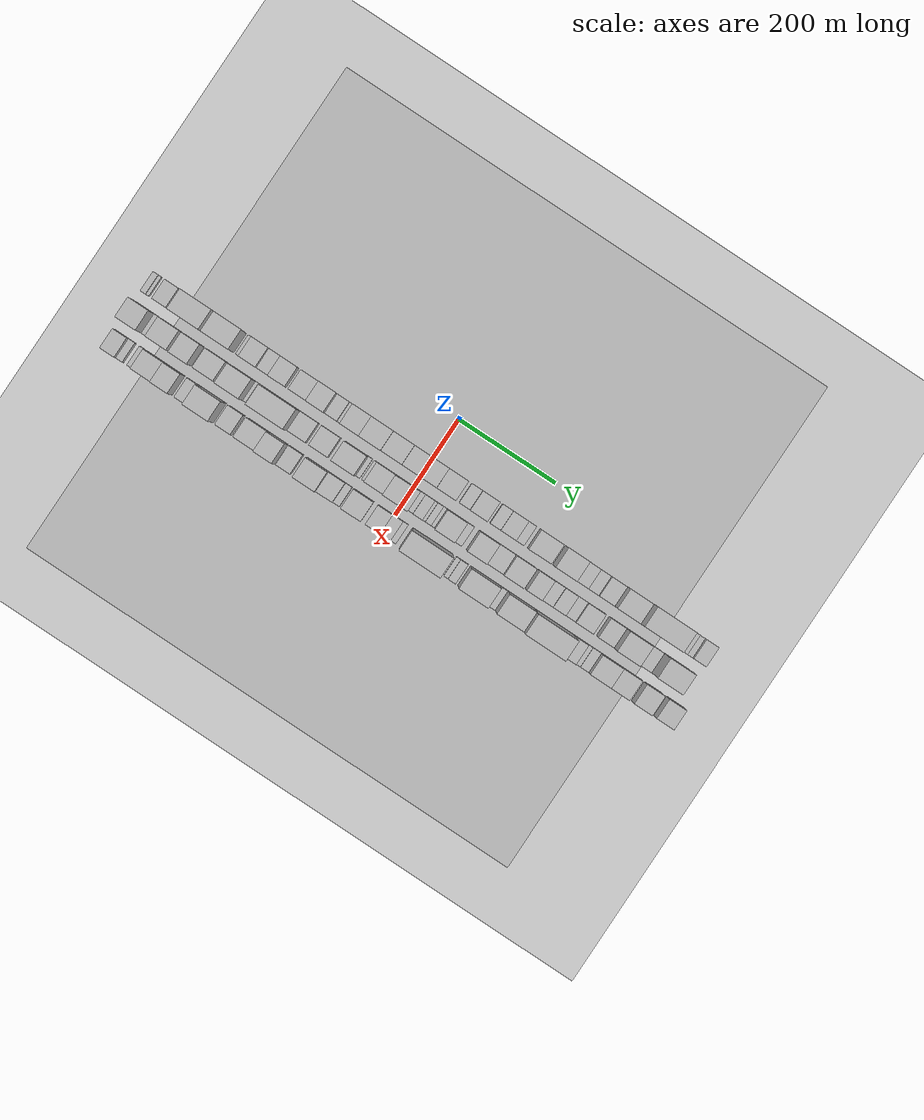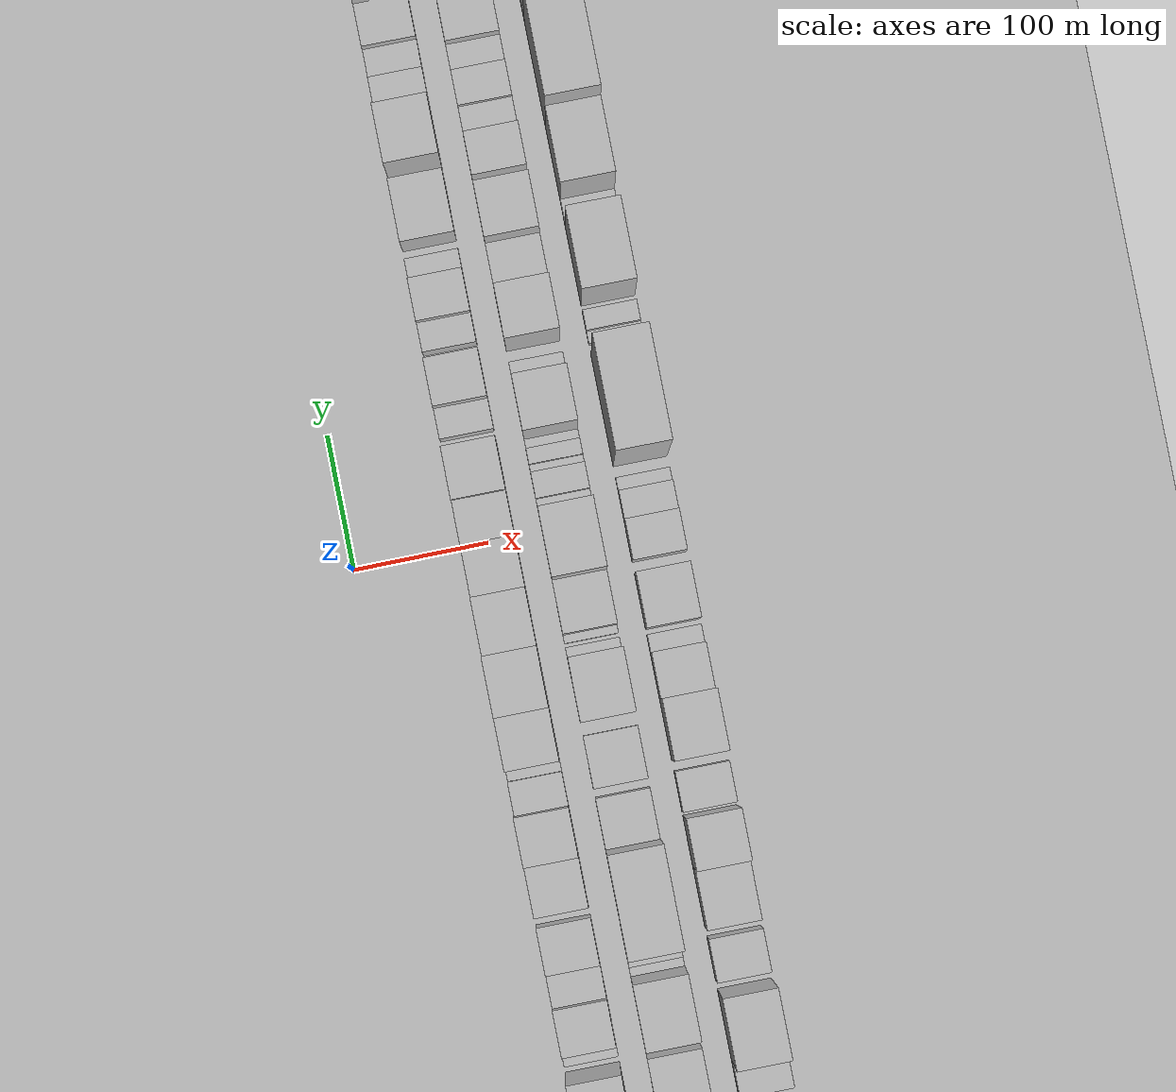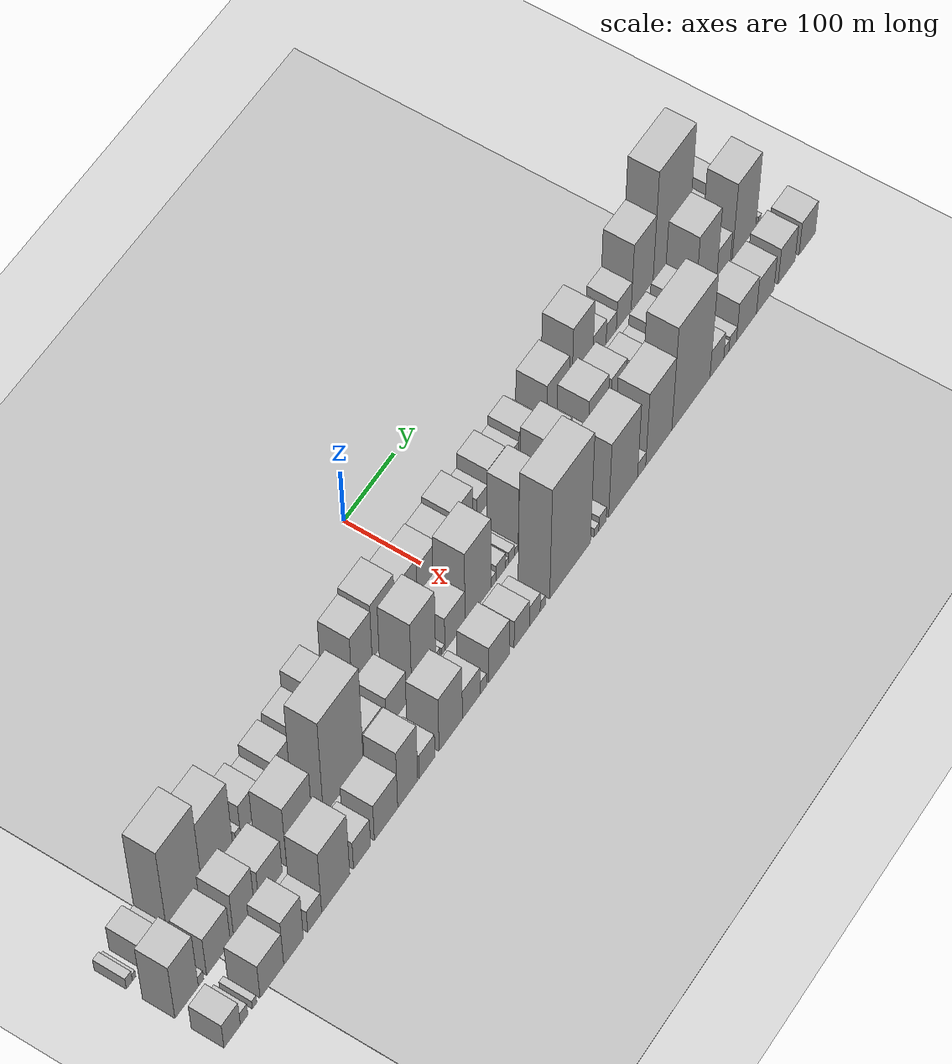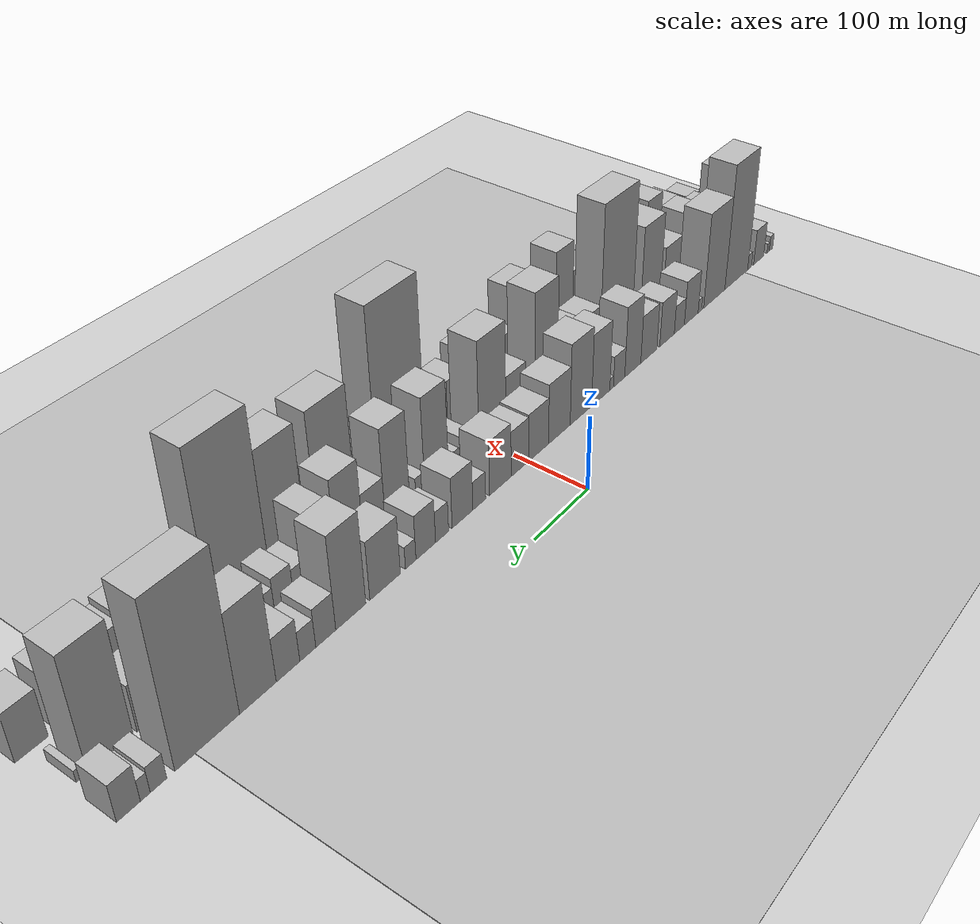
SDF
<?xml version="1.0" encoding="utf-8"?>

<sdf version="1.6">

   <world name="default">

      <gui fullscreen="0">

         <camera name="user_camera">

            <pose>-15 0 4.57585 0 0 0</pose>

            <view_controller>orbit</view_controller>

         </camera>

      </gui>

      <scene>

         <sky>

           <clouds>

             <speed>12</speed>

           </clouds>

         </sky>

         <ambient>0.4 0.4 0.4 1</ambient>

         <background>0.7 0.7 0.7 1</background>

         <shadows>1</shadows>

      </scene>

      <gravity>0 0 -9.8066</gravity>

      <magnetic_field>6e-06 2.3e-05 -4.2e-05</magnetic_field>

      <physics default="0" name="default_physics" type="ode">

         <ode>

            <solver>

               <type>quick</type>

               <iters>10</iters>

               <sor>1.0</sor>

               <use_dynamic_moi_rescaling>0</use_dynamic_moi_rescaling>

            </solver>

            <constraints>

               <cfm>0</cfm>

               <erp>0.2</erp>

               <contact_max_correcting_vel>100</contact_max_correcting_vel>

               <contact_surface_layer>0.001</contact_surface_layer>

            </constraints>

         </ode>

         <max_step_size>0.004</max_step_size>

         <real_time_factor>1</real_time_factor>

         <real_time_update_rate>250</real_time_update_rate>

      </physics>

      <light name="sun" type="directional">

         <cast_shadows>1</cast_shadows>

         <pose>0 0 10 0 0 0</pose>

         <diffuse>0.8 0.8 0.8 1</diffuse>

         <specular>0.2 0.2 0.2 1</specular>

         <attenuation>

            <range>1000</range>

            <constant>0.9</constant>

            <linear>0.01</linear>

            <quadratic>0.001</quadratic>

         </attenuation>

         <direction>-0.5 0.1 -0.9</direction>

      </light>

      <include>

         <name>ground_plane_1</name>

         <uri>model://HANNAS_ground_plane</uri>

         <pose>0 0 0  0 0 0</pose>

      </include>

      <include>

         <name>ground_plane_2</name>

         <uri>model://HANNAS_ground_plane</uri>

         <pose>100 0 0  0 0 0</pose>

      </include>

      <model name="building_1">

         <static>1</static>

         <pose frame="">100.0000 -574.6569 0 0.000000 0.000000 0.000000</pose>

         <link name="link">

            <pose frame="">0 0 12.00 0 0 0</pose>

            <collision name="collision">

               <geometry>

                  <box>

                     <size>40.0000 10.6862 24.0000</size>

                  </box>

               </geometry>

               <max_contacts>10</max_contacts>

               <surface>

                  <contact>

                     <ode/>

                  </contact>

                  <bounce/>

                  <friction>

                     <torsional>

                        <ode/>

                     </torsional>

                     <ode/>

                  </friction>

               </surface>

            </collision>

            <visual name="visual">

               <cast_shadows>0</cast_shadows>

               <geometry>

                  <box>

                     <size>40.0000 10.6862 24.0000</size>

                  </box>

               </geometry>

               <material>

                  <script>

                     <uri>model://HANNAS_wall/materials/scripts</uri>

                     <uri>model://HANNAS_wall/materials/textures</uri>

                     <name>vrc/HANNAS_wall</name>

                  </script>

               </material>

            </visual>

            <self_collide>0</self_collide>

            <enable_wind>0</enable_wind>

            <kinematic>0</kinematic>

         </link>

      </model>

      <model name="building_2">

         <static>1</static>

         <pose frame="">100.0000 -566.2975 0 0.000000 0.000000 0.000000</pose>

         <link name="link">

            <pose frame="">0 0 7.50 0 0 0</pose>

            <collision name="collision">

               <geometry>

                  <box>

                     <size>40.0000 6.0326 15.0000</size>

                  </box>

               </geometry>

               <max_contacts>10</max_contacts>

               <surface>

                  <contact>

                     <ode/>

                  </contact>

                  <bounce/>

                  <friction>

                     <torsional>

                        <ode/>

                     </torsional>

                     <ode/>

                  </friction>

               </surface>

            </collision>

            <visual name="visual">

               <cast_shadows>0</cast_shadows>

               <geometry>

                  <box>

                     <size>40.0000 6.0326 15.0000</size>

                  </box>

               </geometry>

               <material>

                  <script>

                     <uri>model://HANNAS_wall/materials/scripts</uri>

                     <uri>model://HANNAS_wall/materials/textures</uri>

                     <name>vrc/HANNAS_wall</name>

                  </script>

               </material>

            </visual>

            <self_collide>0</self_collide>

            <enable_wind>0</enable_wind>

            <kinematic>0</kinematic>

         </link>

      </model>

      <model name="building_3">

         <static>1</static>

         <pose frame="">100.0000 -538.7408 0 0.000000 0.000000 0.000000</pose>

         <link name="link">

            <pose frame="">0 0 27.00 0 0 0</pose>

            <collision name="collision">

               <geometry>

                  <box>

                     <size>40.0000 29.0807 54.0000</size>

                  </box>

               </geometry>

               <max_contacts>10</max_contacts>

               <surface>

                  <contact>

                     <ode/>

                  </contact>

                  <bounce/>

                  <friction>

                     <torsional>

                        <ode/>

                     </torsional>

                     <ode/>

                  </friction>

               </surface>

            </collision>

            <visual name="visual">

               <cast_shadows>0</cast_shadows>

               <geometry>

                  <box>

                     <size>40.0000 29.0807 54.0000</size>

                  </box>

               </geometry>

               <material>

                  <script>

                     <uri>model://HANNAS_wall/materials/scripts</uri>

                     <uri>model://HANNAS_wall/materials/textures</uri>

                     <name>vrc/HANNAS_wall</name>

                  </script>

               </material>

            </visual>

            <self_collide>0</self_collide>

            <enable_wind>0</enable_wind>

            <kinematic>0</kinematic>

         </link>

      </model>

      <model name="building_4">

         <static>1</static>

         <pose frame="">100.0000 -512.7264 0 0.000000 0.000000 0.000000</pose>

         <link name="link">

            <pose frame="">0 0 12.00 0 0 0</pose>

            <collision name="collision">

               <geometry>

                  <box>

                     <size>40.0000 10.9481 24.0000</size>

                  </box>

               </geometry>

               <max_contacts>10</max_contacts>

               <surface>

                  <contact>

                     <ode/>

                  </contact>

                  <bounce/>

                  <friction>

                     <torsional>

                        <ode/>

                     </torsional>

                     <ode/>

                  </friction>

               </surface>

            </collision>

            <visual name="visual">

               <cast_shadows>0</cast_shadows>

               <geometry>

                  <box>

                     <size>40.0000 10.9481 24.0000</size>

                  </box>

               </geometry>

               <material>

                  <script>

                     <uri>model://HANNAS_wall/materials/scripts</uri>

                     <uri>model://HANNAS_wall/materials/textures</uri>

                     <name>vrc/HANNAS_wall</name>

                  </script>

               </material>

            </visual>

            <self_collide>0</self_collide>

            <enable_wind>0</enable_wind>

            <kinematic>0</kinematic>

         </link>

      </model>

      <model name="building_5">

         <static>1</static>

         <pose frame="">100.0000 -475.8519 0 0.000000 0.000000 0.000000</pose>

         <link name="link">

            <pose frame="">0 0 93.00 0 0 0</pose>

            <collision name="collision">

               <geometry>

                  <box>

                     <size>40.0000 62.8010 186.0000</size>

                  </box>

               </geometry>

               <max_contacts>10</max_contacts>

               <surface>

                  <contact>

                     <ode/>

                  </contact>

                  <bounce/>

                  <friction>

                     <torsional>

                        <ode/>

                     </torsional>

                     <ode/>

                  </friction>

               </surface>

            </collision>

            <visual name="visual">

               <cast_shadows>0</cast_shadows>

               <geometry>

                  <box>

                     <size>40.0000 62.8010 186.0000</size>

                  </box>

               </geometry>

               <material>

                  <script>

                     <uri>model://HANNAS_wall/materials/scripts</uri>

                     <uri>model://HANNAS_wall/materials/textures</uri>

                     <name>vrc/HANNAS_wall</name>

                  </script>

               </material>

            </visual>

            <self_collide>0</self_collide>

            <enable_wind>0</enable_wind>

            <kinematic>0</kinematic>

         </link>

      </model>

      <model name="building_6">

         <static>1</static>

         <pose frame="">100.0000 -416.3720 0 0.000000 0.000000 0.000000</pose>

         <link name="link">

            <pose frame="">0 0 70.50 0 0 0</pose>

            <collision name="collision">

               <geometry>

                  <box>

                     <size>40.0000 56.1587 141.0000</size>

                  </box>

               </geometry>

               <max_contacts>10</max_contacts>

               <surface>

                  <contact>

                     <ode/>

                  </contact>

                  <bounce/>

                  <friction>

                     <torsional>

                        <ode/>

                     </torsional>

                     <ode/>

                  </friction>

               </surface>

            </collision>

            <visual name="visual">

               <cast_shadows>0</cast_shadows>

               <geometry>

                  <box>

                     <size>40.0000 56.1587 141.0000</size>

                  </box>

               </geometry>

               <material>

                  <script>

                     <uri>model://HANNAS_wall/materials/scripts</uri>

                     <uri>model://HANNAS_wall/materials/textures</uri>

                     <name>vrc/HANNAS_wall</name>

                  </script>

               </material>

            </visual>

            <self_collide>0</self_collide>

            <enable_wind>0</enable_wind>

            <kinematic>0</kinematic>

         </link>

      </model>

      <model name="building_7">

         <static>1</static>

         <pose frame="">100.0000 -378.6573 0 0.000000 0.000000 0.000000</pose>

         <link name="link">

            <pose frame="">0 0 10.50 0 0 0</pose>

            <collision name="collision">

               <geometry>

                  <box>

                     <size>40.0000 9.2706 21.0000</size>

                  </box>

               </geometry>

               <max_contacts>10</max_contacts>

               <surface>

                  <contact>

                     <ode/>

                  </contact>

                  <bounce/>

                  <friction>

                     <torsional>

                        <ode/>

                     </torsional>

                     <ode/>

                  </friction>

               </surface>

            </collision>

            <visual name="visual">

               <cast_shadows>0</cast_shadows>

               <geometry>

                  <box>

                     <size>40.0000 9.2706 21.0000</size>

                  </box>

               </geometry>

               <material>

                  <script>

                     <uri>model://HANNAS_wall/materials/scripts</uri>

                     <uri>model://HANNAS_wall/materials/textures</uri>

                     <name>vrc/HANNAS_wall</name>

                  </script>

               </material>

            </visual>

            <self_collide>0</self_collide>

            <enable_wind>0</enable_wind>

            <kinematic>0</kinematic>

         </link>

      </model>

      <model name="building_8">

         <static>1</static>

         <pose frame="">100.0000 -356.5985 0 0.000000 0.000000 0.000000</pose>

         <link name="link">

            <pose frame="">0 0 33.00 0 0 0</pose>

            <collision name="collision">

               <geometry>

                  <box>

                     <size>40.0000 34.8471 66.0000</size>

                  </box>

               </geometry>

               <max_contacts>10</max_contacts>

               <surface>

                  <contact>

                     <ode/>

                  </contact>

                  <bounce/>

                  <friction>

                     <torsional>

                        <ode/>

                     </torsional>

                     <ode/>

                  </friction>

               </surface>

            </collision>

            <visual name="visual">

               <cast_shadows>0</cast_shadows>

               <geometry>

                  <box>

                     <size>40.0000 34.8471 66.0000</size>

                  </box>

               </geometry>

               <material>

                  <script>

                     <uri>model://HANNAS_wall/materials/scripts</uri>

                     <uri>model://HANNAS_wall/materials/textures</uri>

                     <name>vrc/HANNAS_wall</name>

                  </script>

               </material>

            </visual>

            <self_collide>0</self_collide>

            <enable_wind>0</enable_wind>

            <kinematic>0</kinematic>

         </link>

      </model>

      <model name="building_9">

         <static>1</static>

         <pose frame="">100.0000 -326.7588 0 0.000000 0.000000 0.000000</pose>

         <link name="link">

            <pose frame="">0 0 21.00 0 0 0</pose>

            <collision name="collision">

               <geometry>

                  <box>

                     <size>40.0000 24.8324 42.0000</size>

                  </box>

               </geometry>

               <max_contacts>10</max_contacts>

               <surface>

                  <contact>

                     <ode/>

                  </contact>

                  <bounce/>

                  <friction>

                     <torsional>

                        <ode/>

                     </torsional>

                     <ode/>

                  </friction>

               </surface>

            </collision>

            <visual name="visual">

               <cast_shadows>0</cast_shadows>

               <geometry>

                  <box>

                     <size>40.0000 24.8324 42.0000</size>

                  </box>

               </geometry>

               <material>

                  <script>

                     <uri>model://HANNAS_wall/materials/scripts</uri>

                     <uri>model://HANNAS_wall/materials/textures</uri>

                     <name>vrc/HANNAS_wall</name>

                  </script>

               </material>

            </visual>

            <self_collide>0</self_collide>

            <enable_wind>0</enable_wind>

            <kinematic>0</kinematic>

         </link>

      </model>

      <model name="building_10">

         <static>1</static>

         <pose frame="">100.0000 -296.7692 0 0.000000 0.000000 0.000000</pose>

         <link name="link">

            <pose frame="">0 0 33.00 0 0 0</pose>

            <collision name="collision">

               <geometry>

                  <box>

                     <size>40.0000 35.1467 66.0000</size>

                  </box>

               </geometry>

               <max_contacts>10</max_contacts>

               <surface>

                  <contact>

                     <ode/>

                  </contact>

                  <bounce/>

                  <friction>

                     <torsional>

                        <ode/>

                     </torsional>

                     <ode/>

                  </friction>

               </surface>

            </collision>

            <visual name="visual">

               <cast_shadows>0</cast_shadows>

               <geometry>

                  <box>

                     <size>40.0000 35.1467 66.0000</size>

                  </box>

               </geometry>

               <material>

                  <script>

                     <uri>model://HANNAS_wall/materials/scripts</uri>

                     <uri>model://HANNAS_wall/materials/textures</uri>

                     <name>vrc/HANNAS_wall</name>

                  </script>

               </material>

            </visual>

            <self_collide>0</self_collide>

            <enable_wind>0</enable_wind>

            <kinematic>0</kinematic>

         </link>

      </model>

      <model name="building_11">

         <static>1</static>

         <pose frame="">100.0000 -253.4089 0 0.000000 0.000000 0.000000</pose>

         <link name="link">

            <pose frame="">0 0 34.50 0 0 0</pose>

            <collision name="collision">

               <geometry>

                  <box>

                     <size>40.0000 37.5741 69.0000</size>

                  </box>

               </geometry>

               <max_contacts>10</max_contacts>

               <surface>

                  <contact>

                     <ode/>

                  </contact>

                  <bounce/>

                  <friction>

                     <torsional>

                        <ode/>

                     </torsional>

                     <ode/>

                  </friction>

               </surface>

            </collision>

            <visual name="visual">

               <cast_shadows>0</cast_shadows>

               <geometry>

                  <box>

                     <size>40.0000 37.5741 69.0000</size>

                  </box>

               </geometry>

               <material>

                  <script>

                     <uri>model://HANNAS_wall/materials/scripts</uri>

                     <uri>model://HANNAS_wall/materials/textures</uri>

                     <name>vrc/HANNAS_wall</name>

                  </script>

               </material>

            </visual>

            <self_collide>0</self_collide>

            <enable_wind>0</enable_wind>

            <kinematic>0</kinematic>

         </link>

      </model>

      <model name="building_12">

         <static>1</static>

         <pose frame="">100.0000 -216.4043 0 0.000000 0.000000 0.000000</pose>

         <link name="link">

            <pose frame="">0 0 51.00 0 0 0</pose>

            <collision name="collision">

               <geometry>

                  <box>

                     <size>40.0000 36.4351 102.0000</size>

                  </box>

               </geometry>

               <max_contacts>10</max_contacts>

               <surface>

                  <contact>

                     <ode/>

                  </contact>

                  <bounce/>

                  <friction>

                     <torsional>

                        <ode/>

                     </torsional>

                     <ode/>

                  </friction>

               </surface>

            </collision>

            <visual name="visual">

               <cast_shadows>0</cast_shadows>

               <geometry>

                  <box>

                     <size>40.0000 36.4351 102.0000</size>

                  </box>

               </geometry>

               <material>

                  <script>

                     <uri>model://HANNAS_wall/materials/scripts</uri>

                     <uri>model://HANNAS_wall/materials/textures</uri>

                     <name>vrc/HANNAS_wall</name>

                  </script>

               </material>

            </visual>

            <self_collide>0</self_collide>

            <enable_wind>0</enable_wind>

            <kinematic>0</kinematic>

         </link>

      </model>

      <model name="building_13">

         <static>1</static>

         <pose frame="">100.0000 -185.5841 0 0.000000 0.000000 0.000000</pose>

         <link name="link">

            <pose frame="">0 0 22.50 0 0 0</pose>

            <collision name="collision">

               <geometry>

                  <box>

                     <size>40.0000 25.2053 45.0000</size>

                  </box>

               </geometry>

               <max_contacts>10</max_contacts>

               <surface>

                  <contact>

                     <ode/>

                  </contact>

                  <bounce/>

                  <friction>

                     <torsional>

                        <ode/>

                     </torsional>

                     <ode/>

                  </friction>

               </surface>

            </collision>

            <visual name="visual">

               <cast_shadows>0</cast_shadows>

               <geometry>

                  <box>

                     <size>40.0000 25.2053 45.0000</size>

                  </box>

               </geometry>

               <material>

                  <script>

                     <uri>model://HANNAS_wall/materials/scripts</uri>

                     <uri>model://HANNAS_wall/materials/textures</uri>

                     <name>vrc/HANNAS_wall</name>

                  </script>

               </material>

            </visual>

            <self_collide>0</self_collide>

            <enable_wind>0</enable_wind>

            <kinematic>0</kinematic>

         </link>

      </model>

      <model name="building_14">

         <static>1</static>

         <pose frame="">100.0000 -169.0325 0 0.000000 0.000000 0.000000</pose>

         <link name="link">

            <pose frame="">0 0 9.00 0 0 0</pose>

            <collision name="collision">

               <geometry>

                  <box>

                     <size>40.0000 7.8978 18.0000</size>

                  </box>

               </geometry>

               <max_contacts>10</max_contacts>

               <surface>

                  <contact>

                     <ode/>

                  </contact>

                  <bounce/>

                  <friction>

                     <torsional>

                        <ode/>

                     </torsional>

                     <ode/>

                  </friction>

               </surface>

            </collision>

            <visual name="visual">

               <cast_shadows>0</cast_shadows>

               <geometry>

                  <box>

                     <size>40.0000 7.8978 18.0000</size>

                  </box>

               </geometry>

               <material>

                  <script>

                     <uri>model://HANNAS_wall/materials/scripts</uri>

                     <uri>model://HANNAS_wall/materials/textures</uri>

                     <name>vrc/HANNAS_wall</name>

                  </script>

               </material>

            </visual>

            <self_collide>0</self_collide>

            <enable_wind>0</enable_wind>

            <kinematic>0</kinematic>

         </link>

      </model>

      <model name="building_15">

         <static>1</static>

         <pose frame="">100.0000 -145.6583 0 0.000000 0.000000 0.000000</pose>

         <link name="link">

            <pose frame="">0 0 51.00 0 0 0</pose>

            <collision name="collision">

               <geometry>

                  <box>

                     <size>40.0000 38.8507 102.0000</size>

                  </box>

               </geometry>

               <max_contacts>10</max_contacts>

               <surface>

                  <contact>

                     <ode/>

                  </contact>

                  <bounce/>

                  <friction>

                     <torsional>

                        <ode/>

                     </torsional>

                     <ode/>

                  </friction>

               </surface>

            </collision>

            <visual name="visual">

               <cast_shadows>0</cast_shadows>

               <geometry>

                  <box>

                     <size>40.0000 38.8507 102.0000</size>

                  </box>

               </geometry>

               <material>

                  <script>

                     <uri>model://HANNAS_wall/materials/scripts</uri>

                     <uri>model://HANNAS_wall/materials/textures</uri>

                     <name>vrc/HANNAS_wall</name>

                  </script>

               </material>

            </visual>

            <self_collide>0</self_collide>

            <enable_wind>0</enable_wind>

            <kinematic>0</kinematic>

         </link>

      </model>

      <model name="building_16">

         <static>1</static>

         <pose frame="">100.0000 -103.8795 0 0.000000 0.000000 0.000000</pose>

         <link name="link">

            <pose frame="">0 0 57.00 0 0 0</pose>

            <collision name="collision">

               <geometry>

                  <box>

                     <size>40.0000 44.7068 114.0000</size>

                  </box>

               </geometry>

               <max_contacts>10</max_contacts>

               <surface>

                  <contact>

                     <ode/>

                  </contact>

                  <bounce/>

                  <friction>

                     <torsional>

                        <ode/>

                     </torsional>

                     <ode/>

                  </friction>

               </surface>

            </collision>

            <visual name="visual">

               <cast_shadows>0</cast_shadows>

               <geometry>

                  <box>

                     <size>40.0000 44.7068 114.0000</size>

                  </box>

               </geometry>

               <material>

                  <script>

                     <uri>model://HANNAS_wall/materials/scripts</uri>

                     <uri>model://HANNAS_wall/materials/textures</uri>

                     <name>vrc/HANNAS_wall</name>

                  </script>

               </material>

            </visual>

            <self_collide>0</self_collide>

            <enable_wind>0</enable_wind>

            <kinematic>0</kinematic>

         </link>

      </model>

      <model name="building_17">

         <static>1</static>

         <pose frame="">100.0000 -59.8628 0 0.000000 0.000000 0.000000</pose>

         <link name="link">

            <pose frame="">0 0 42.00 0 0 0</pose>

            <collision name="collision">

               <geometry>

                  <box>

                     <size>40.0000 43.3265 84.0000</size>

                  </box>

               </geometry>

               <max_contacts>10</max_contacts>

               <surface>

                  <contact>

                     <ode/>

                  </contact>

                  <bounce/>

                  <friction>

                     <torsional>

                        <ode/>

                     </torsional>

                     <ode/>

                  </friction>

               </surface>

            </collision>

            <visual name="visual">

               <cast_shadows>0</cast_shadows>

               <geometry>

                  <box>

                     <size>40.0000 43.3265 84.0000</size>

                  </box>

               </geometry>

               <material>

                  <script>

                     <uri>model://HANNAS_wall/materials/scripts</uri>

                     <uri>model://HANNAS_wall/materials/textures</uri>

                     <name>vrc/HANNAS_wall</name>

                  </script>

               </material>

            </visual>

            <self_collide>0</self_collide>

            <enable_wind>0</enable_wind>

            <kinematic>0</kinematic>

         </link>

      </model>

      <model name="building_18">

         <static>1</static>

         <pose frame="">100.0000 -19.0038 0 0.000000 0.000000 0.000000</pose>

         <link name="link">

            <pose frame="">0 0 33.00 0 0 0</pose>

            <collision name="collision">

               <geometry>

                  <box>

                     <size>40.0000 38.3915 66.0000</size>

                  </box>

               </geometry>

               <max_contacts>10</max_contacts>

               <surface>

                  <contact>

                     <ode/>

                  </contact>

                  <bounce/>

                  <friction>

                     <torsional>

                        <ode/>

                     </torsional>

                     <ode/>

                  </friction>

               </surface>

            </collision>

            <visual name="visual">

               <cast_shadows>0</cast_shadows>

               <geometry>

                  <box>

                     <size>40.0000 38.3915 66.0000</size>

                  </box>

               </geometry>

               <material>

                  <script>

                     <uri>model://HANNAS_wall/materials/scripts</uri>

                     <uri>model://HANNAS_wall/materials/textures</uri>

                     <name>vrc/HANNAS_wall</name>

                  </script>

               </material>

            </visual>

            <self_collide>0</self_collide>

            <enable_wind>0</enable_wind>

            <kinematic>0</kinematic>

         </link>

      </model>

      <model name="building_19">

         <static>1</static>

         <pose frame="">100.0000 16.6718 0 0.000000 0.000000 0.000000</pose>

         <link name="link">

            <pose frame="">0 0 31.50 0 0 0</pose>

            <collision name="collision">

               <geometry>

                  <box>

                     <size>40.0000 32.9597 63.0000</size>

                  </box>

               </geometry>

               <max_contacts>10</max_contacts>

               <surface>

                  <contact>

                     <ode/>

                  </contact>

                  <bounce/>

                  <friction>

                     <torsional>

                        <ode/>

                     </torsional>

                     <ode/>

                  </friction>

               </surface>

            </collision>

            <visual name="visual">

               <cast_shadows>0</cast_shadows>

               <geometry>

                  <box>

                     <size>40.0000 32.9597 63.0000</size>

                  </box>

               </geometry>

               <material>

                  <script>

                     <uri>model://HANNAS_wall/materials/scripts</uri>

                     <uri>model://HANNAS_wall/materials/textures</uri>

                     <name>vrc/HANNAS_wall</name>

                  </script>

               </material>

            </visual>

            <self_collide>0</self_collide>

            <enable_wind>0</enable_wind>

            <kinematic>0</kinematic>

         </link>

      </model>

      <model name="building_20">

         <static>1</static>

         <pose frame="">100.0000 52.8334 0 0.000000 0.000000 0.000000</pose>

         <link name="link">

            <pose frame="">0 0 37.50 0 0 0</pose>

            <collision name="collision">

               <geometry>

                  <box>

                     <size>40.0000 39.3635 75.0000</size>

                  </box>

               </geometry>

               <max_contacts>10</max_contacts>

               <surface>

                  <contact>

                     <ode/>

                  </contact>

                  <bounce/>

                  <friction>

                     <torsional>

                        <ode/>

                     </torsional>

                     <ode/>

                  </friction>

               </surface>

            </collision>

            <visual name="visual">

               <cast_shadows>0</cast_shadows>

               <geometry>

                  <box>

                     <size>40.0000 39.3635 75.0000</size>

                  </box>

               </geometry>

               <material>

                  <script>

                     <uri>model://HANNAS_wall/materials/scripts</uri>

                     <uri>model://HANNAS_wall/materials/textures</uri>

                     <name>vrc/HANNAS_wall</name>

                  </script>

               </material>

            </visual>

            <self_collide>0</self_collide>

            <enable_wind>0</enable_wind>

            <kinematic>0</kinematic>

         </link>

      </model>

      <model name="building_21">

         <static>1</static>

         <pose frame="">100.0000 90.7541 0 0.000000 0.000000 0.000000</pose>

         <link name="link">

            <pose frame="">0 0 19.50 0 0 0</pose>

            <collision name="collision">

               <geometry>

                  <box>

                     <size>40.0000 22.4779 39.0000</size>

                  </box>

               </geometry>

               <max_contacts>10</max_contacts>

               <surface>

                  <contact>

                     <ode/>

                  </contact>

                  <bounce/>

                  <friction>

                     <torsional>

                        <ode/>

                     </torsional>

                     <ode/>

                  </friction>

               </surface>

            </collision>

            <visual name="visual">

               <cast_shadows>0</cast_shadows>

               <geometry>

                  <box>

                     <size>40.0000 22.4779 39.0000</size>

                  </box>

               </geometry>

               <material>

                  <script>

                     <uri>model://HANNAS_wall/materials/scripts</uri>

                     <uri>model://HANNAS_wall/materials/textures</uri>

                     <name>vrc/HANNAS_wall</name>

                  </script>

               </material>

            </visual>

            <self_collide>0</self_collide>

            <enable_wind>0</enable_wind>

            <kinematic>0</kinematic>

         </link>

      </model>

      <model name="building_22">

         <static>1</static>

         <pose frame="">100.0000 119.7571 0 0.000000 0.000000 0.000000</pose>

         <link name="link">

            <pose frame="">0 0 34.50 0 0 0</pose>

            <collision name="collision">

               <geometry>

                  <box>

                     <size>40.0000 35.5280 69.0000</size>

                  </box>

               </geometry>

               <max_contacts>10</max_contacts>

               <surface>

                  <contact>

                     <ode/>

                  </contact>

                  <bounce/>

                  <friction>

                     <torsional>

                        <ode/>

                     </torsional>

                     <ode/>

                  </friction>

               </surface>

            </collision>

            <visual name="visual">

               <cast_shadows>0</cast_shadows>

               <geometry>

                  <box>

                     <size>40.0000 35.5280 69.0000</size>

                  </box>

               </geometry>

               <material>

                  <script>

                     <uri>model://HANNAS_wall/materials/scripts</uri>

                     <uri>model://HANNAS_wall/materials/textures</uri>

                     <name>vrc/HANNAS_wall</name>

                  </script>

               </material>

            </visual>

            <self_collide>0</self_collide>

            <enable_wind>0</enable_wind>

            <kinematic>0</kinematic>

         </link>

      </model>

      <model name="building_23">

         <static>1</static>

         <pose frame="">100.0000 154.3100 0 0.000000 0.000000 0.000000</pose>

         <link name="link">

            <pose frame="">0 0 21.00 0 0 0</pose>

            <collision name="collision">

               <geometry>

                  <box>

                     <size>40.0000 21.5779 42.0000</size>

                  </box>

               </geometry>

               <max_contacts>10</max_contacts>

               <surface>

                  <contact>

                     <ode/>

                  </contact>

                  <bounce/>

                  <friction>

                     <torsional>

                        <ode/>

                     </torsional>

                     <ode/>

                  </friction>

               </surface>

            </collision>

            <visual name="visual">

               <cast_shadows>0</cast_shadows>

               <geometry>

                  <box>

                     <size>40.0000 21.5779 42.0000</size>

                  </box>

               </geometry>

               <material>

                  <script>

                     <uri>model://HANNAS_wall/materials/scripts</uri>

                     <uri>model://HANNAS_wall/materials/textures</uri>

                     <name>vrc/HANNAS_wall</name>

                  </script>

               </material>

            </visual>

            <self_collide>0</self_collide>

            <enable_wind>0</enable_wind>

            <kinematic>0</kinematic>

         </link>

      </model>

      <model name="building_24">

         <static>1</static>

         <pose frame="">100.0000 180.9604 0 0.000000 0.000000 0.000000</pose>

         <link name="link">

            <pose frame="">0 0 30.00 0 0 0</pose>

            <collision name="collision">

               <geometry>

                  <box>

                     <size>40.0000 31.7229 60.0000</size>

                  </box>

               </geometry>

               <max_contacts>10</max_contacts>

               <surface>

                  <contact>

                     <ode/>

                  </contact>

                  <bounce/>

                  <friction>

                     <torsional>

                        <ode/>

                     </torsional>

                     <ode/>

                  </friction>

               </surface>

            </collision>

            <visual name="visual">

               <cast_shadows>0</cast_shadows>

               <geometry>

                  <box>

                     <size>40.0000 31.7229 60.0000</size>

                  </box>

               </geometry>

               <material>

                  <script>

                     <uri>model://HANNAS_wall/materials/scripts</uri>

                     <uri>model://HANNAS_wall/materials/textures</uri>

                     <name>vrc/HANNAS_wall</name>

                  </script>

               </material>

            </visual>

            <self_collide>0</self_collide>

            <enable_wind>0</enable_wind>

            <kinematic>0</kinematic>

         </link>

      </model>

      <model name="building_25">

         <static>1</static>

         <pose frame="">100.0000 205.2164 0 0.000000 0.000000 0.000000</pose>

         <link name="link">

            <pose frame="">0 0 15.00 0 0 0</pose>

            <collision name="collision">

               <geometry>

                  <box>

                     <size>40.0000 16.7892 30.0000</size>

                  </box>

               </geometry>

               <max_contacts>10</max_contacts>

               <surface>

                  <contact>

                     <ode/>

                  </contact>

                  <bounce/>

                  <friction>

                     <torsional>

                        <ode/>

                     </torsional>

                     <ode/>

                  </friction>

               </surface>

            </collision>

            <visual name="visual">

               <cast_shadows>0</cast_shadows>

               <geometry>

                  <box>

                     <size>40.0000 16.7892 30.0000</size>

                  </box>

               </geometry>

               <material>

                  <script>

                     <uri>model://HANNAS_wall/materials/scripts</uri>

                     <uri>model://HANNAS_wall/materials/textures</uri>

                     <name>vrc/HANNAS_wall</name>

                  </script>

               </material>

            </visual>

            <self_collide>0</self_collide>

            <enable_wind>0</enable_wind>

            <kinematic>0</kinematic>

         </link>

      </model>

      <model name="building_26">

         <static>1</static>

         <pose frame="">100.0000 244.8962 0 0.000000 0.000000 0.000000</pose>

         <link name="link">

            <pose frame="">0 0 39.00 0 0 0</pose>

            <collision name="collision">

               <geometry>

                  <box>

                     <size>40.0000 46.5704 78.0000</size>

                  </box>

               </geometry>

               <max_contacts>10</max_contacts>

               <surface>

                  <contact>

                     <ode/>

                  </contact>

                  <bounce/>

                  <friction>

                     <torsional>

                        <ode/>

                     </torsional>

                     <ode/>

                  </friction>

               </surface>

            </collision>

            <visual name="visual">

               <cast_shadows>0</cast_shadows>

               <geometry>

                  <box>

                     <size>40.0000 46.5704 78.0000</size>

                  </box>

               </geometry>

               <material>

                  <script>

                     <uri>model://HANNAS_wall/materials/scripts</uri>

                     <uri>model://HANNAS_wall/materials/textures</uri>

                     <name>vrc/HANNAS_wall</name>

                  </script>

               </material>

            </visual>

            <self_collide>0</self_collide>

            <enable_wind>0</enable_wind>

            <kinematic>0</kinematic>

         </link>

      </model>

      <model name="building_27">

         <static>1</static>

         <pose frame="">100.0000 296.0267 0 0.000000 0.000000 0.000000</pose>

         <link name="link">

            <pose frame="">0 0 61.50 0 0 0</pose>

            <collision name="collision">

               <geometry>

                  <box>

                     <size>40.0000 43.6906 123.0000</size>

                  </box>

               </geometry>

               <max_contacts>10</max_contacts>

               <surface>

                  <contact>

                     <ode/>

                  </contact>

                  <bounce/>

                  <friction>

                     <torsional>

                        <ode/>

                     </torsional>

                     <ode/>

                  </friction>

               </surface>

            </collision>

            <visual name="visual">

               <cast_shadows>0</cast_shadows>

               <geometry>

                  <box>

                     <size>40.0000 43.6906 123.0000</size>

                  </box>

               </geometry>

               <material>

                  <script>

                     <uri>model://HANNAS_wall/materials/scripts</uri>

                     <uri>model://HANNAS_wall/materials/textures</uri>

                     <name>vrc/HANNAS_wall</name>

                  </script>

               </material>

            </visual>

            <self_collide>0</self_collide>

            <enable_wind>0</enable_wind>

            <kinematic>0</kinematic>

         </link>

      </model>

      <model name="building_28">

         <static>1</static>

         <pose frame="">100.0000 331.8743 0 0.000000 0.000000 0.000000</pose>

         <link name="link">

            <pose frame="">0 0 25.50 0 0 0</pose>

            <collision name="collision">

               <geometry>

                  <box>

                     <size>40.0000 28.0047 51.0000</size>

                  </box>

               </geometry>

               <max_contacts>10</max_contacts>

               <surface>

                  <contact>

                     <ode/>

                  </contact>

                  <bounce/>

                  <friction>

                     <torsional>

                        <ode/>

                     </torsional>

                     <ode/>

                  </friction>

               </surface>

            </collision>

            <visual name="visual">

               <cast_shadows>0</cast_shadows>

               <geometry>

                  <box>

                     <size>40.0000 28.0047 51.0000</size>

                  </box>

               </geometry>

               <material>

                  <script>

                     <uri>model://HANNAS_wall/materials/scripts</uri>

                     <uri>model://HANNAS_wall/materials/textures</uri>

                     <name>vrc/HANNAS_wall</name>

                  </script>

               </material>

            </visual>

            <self_collide>0</self_collide>

            <enable_wind>0</enable_wind>

            <kinematic>0</kinematic>

         </link>

      </model>

      <model name="building_29">

         <static>1</static>

         <pose frame="">100.0000 356.8069 0 0.000000 0.000000 0.000000</pose>

         <link name="link">

            <pose frame="">0 0 19.50 0 0 0</pose>

            <collision name="collision">

               <geometry>

                  <box>

                     <size>40.0000 21.8605 39.0000</size>

                  </box>

               </geometry>

               <max_contacts>10</max_contacts>

               <surface>

                  <contact>

                     <ode/>

                  </contact>

                  <bounce/>

                  <friction>

                     <torsional>

                        <ode/>

                     </torsional>

                     <ode/>

                  </friction>

               </surface>

            </collision>

            <visual name="visual">

               <cast_shadows>0</cast_shadows>

               <geometry>

                  <box>

                     <size>40.0000 21.8605 39.0000</size>

                  </box>

               </geometry>

               <material>

                  <script>

                     <uri>model://HANNAS_wall/materials/scripts</uri>

                     <uri>model://HANNAS_wall/materials/textures</uri>

                     <name>vrc/HANNAS_wall</name>

                  </script>

               </material>

            </visual>

            <self_collide>0</self_collide>

            <enable_wind>0</enable_wind>

            <kinematic>0</kinematic>

         </link>

      </model>

      <model name="building_30">

         <static>1</static>

         <pose frame="">100.0000 383.3998 0 0.000000 0.000000 0.000000</pose>

         <link name="link">

            <pose frame="">0 0 28.50 0 0 0</pose>

            <collision name="collision">

               <geometry>

                  <box>

                     <size>40.0000 31.3254 57.0000</size>

                  </box>

               </geometry>

               <max_contacts>10</max_contacts>

               <surface>

                  <contact>

                     <ode/>

                  </contact>

                  <bounce/>

                  <friction>

                     <torsional>

                        <ode/>

                     </torsional>

                     <ode/>

                  </friction>

               </surface>

            </collision>

            <visual name="visual">

               <cast_shadows>0</cast_shadows>

               <geometry>

                  <box>

                     <size>40.0000 31.3254 57.0000</size>

                  </box>

               </geometry>

               <material>

                  <script>

                     <uri>model://HANNAS_wall/materials/scripts</uri>

                     <uri>model://HANNAS_wall/materials/textures</uri>

                     <name>vrc/HANNAS_wall</name>

                  </script>

               </material>

            </visual>

            <self_collide>0</self_collide>

            <enable_wind>0</enable_wind>

            <kinematic>0</kinematic>

         </link>

      </model>

      <model name="building_31">

         <static>1</static>

         <pose frame="">100.0000 422.5786 0 0.000000 0.000000 0.000000</pose>

         <link name="link">

            <pose frame="">0 0 64.50 0 0 0</pose>

            <collision name="collision">

               <geometry>

                  <box>

                     <size>40.0000 47.0321 129.0000</size>

                  </box>

               </geometry>

               <max_contacts>10</max_contacts>

               <surface>

                  <contact>

                     <ode/>

                  </contact>

                  <bounce/>

                  <friction>

                     <torsional>

                        <ode/>

                     </torsional>

                     <ode/>

                  </friction>

               </surface>

            </collision>

            <visual name="visual">

               <cast_shadows>0</cast_shadows>

               <geometry>

                  <box>

                     <size>40.0000 47.0321 129.0000</size>

                  </box>

               </geometry>

               <material>

                  <script>

                     <uri>model://HANNAS_wall/materials/scripts</uri>

                     <uri>model://HANNAS_wall/materials/textures</uri>

                     <name>vrc/HANNAS_wall</name>

                  </script>

               </material>

            </visual>

            <self_collide>0</self_collide>

            <enable_wind>0</enable_wind>

            <kinematic>0</kinematic>

         </link>

      </model>

      <model name="building_32">

         <static>1</static>

         <pose frame="">100.0000 484.9274 0 0.000000 0.000000 0.000000</pose>

         <link name="link">

            <pose frame="">0 0 105.00 0 0 0</pose>

            <collision name="collision">

               <geometry>

                  <box>

                     <size>40.0000 77.6657 210.0000</size>

                  </box>

               </geometry>

               <max_contacts>10</max_contacts>

               <surface>

                  <contact>

                     <ode/>

                  </contact>

                  <bounce/>

                  <friction>

                     <torsional>

                        <ode/>

                     </torsional>

                     <ode/>

                  </friction>

               </surface>

            </collision>

            <visual name="visual">

               <cast_shadows>0</cast_shadows>

               <geometry>

                  <box>

                     <size>40.0000 77.6657 210.0000</size>

                  </box>

               </geometry>

               <material>

                  <script>

                     <uri>model://HANNAS_wall/materials/scripts</uri>

                     <uri>model://HANNAS_wall/materials/textures</uri>

                     <name>vrc/HANNAS_wall</name>

                  </script>

               </material>

            </visual>

            <self_collide>0</self_collide>

            <enable_wind>0</enable_wind>

            <kinematic>0</kinematic>

         </link>

      </model>

      <model name="building_33">

         <static>1</static>

         <pose frame="">100.0000 542.0718 0 0.000000 0.000000 0.000000</pose>

         <link name="link">

            <pose frame="">0 0 16.50 0 0 0</pose>

            <collision name="collision">

               <geometry>

                  <box>

                     <size>40.0000 18.6230 33.0000</size>

                  </box>

               </geometry>

               <max_contacts>10</max_contacts>

               <surface>

                  <contact>

                     <ode/>

                  </contact>

                  <bounce/>

                  <friction>

                     <torsional>

                        <ode/>

                     </torsional>

                     <ode/>

                  </friction>

               </surface>

            </collision>

            <visual name="visual">

               <cast_shadows>0</cast_shadows>

               <geometry>

                  <box>

                     <size>40.0000 18.6230 33.0000</size>

                  </box>

               </geometry>

               <material>

                  <script>

                     <uri>model://HANNAS_wall/materials/scripts</uri>

                     <uri>model://HANNAS_wall/materials/textures</uri>

                     <name>vrc/HANNAS_wall</name>

                  </script>

               </material>

            </visual>

            <self_collide>0</self_collide>

            <enable_wind>0</enable_wind>

            <kinematic>0</kinematic>

         </link>

      </model>

      <model name="building_34">

         <static>1</static>

         <pose frame="">100.0000 556.8695 0 0.000000 0.000000 0.000000</pose>

         <link name="link">

            <pose frame="">0 0 13.50 0 0 0</pose>

            <collision name="collision">

               <geometry>

                  <box>

                     <size>40.0000 10.9724 27.0000</size>

                  </box>

               </geometry>

               <max_contacts>10</max_contacts>

               <surface>

                  <contact>

                     <ode/>

                  </contact>

                  <bounce/>

                  <friction>

                     <torsional>

                        <ode/>

                     </torsional>

                     <ode/>

                  </friction>

               </surface>

            </collision>

            <visual name="visual">

               <cast_shadows>0</cast_shadows>

               <geometry>

                  <box>

                     <size>40.0000 10.9724 27.0000</size>

                  </box>

               </geometry>

               <material>

                  <script>

                     <uri>model://HANNAS_wall/materials/scripts</uri>

                     <uri>model://HANNAS_wall/materials/textures</uri>

                     <name>vrc/HANNAS_wall</name>

                  </script>

               </material>

            </visual>

            <self_collide>0</self_collide>

            <enable_wind>0</enable_wind>

            <kinematic>0</kinematic>

         </link>

      </model>

      <model name="building_35">

         <static>1</static>

         <pose frame="">100.0000 575.3546 0 0.000000 0.000000 0.000000</pose>

         <link name="link">

            <pose frame="">0 0 24.00 0 0 0</pose>

            <collision name="collision">

               <geometry>

                  <box>

                     <size>40.0000 25.9978 48.0000</size>

                  </box>

               </geometry>

               <max_contacts>10</max_contacts>

               <surface>

                  <contact>

                     <ode/>

                  </contact>

                  <bounce/>

                  <friction>

                     <torsional>

                        <ode/>

                     </torsional>

                     <ode/>

                  </friction>

               </surface>

            </collision>

            <visual name="visual">

               <cast_shadows>0</cast_shadows>

               <geometry>

                  <box>

                     <size>40.0000 25.9978 48.0000</size>

                  </box>

               </geometry>

               <material>

                  <script>

                     <uri>model://HANNAS_wall/materials/scripts</uri>

                     <uri>model://HANNAS_wall/materials/textures</uri>

                     <name>vrc/HANNAS_wall</name>

                  </script>

               </material>

            </visual>

            <self_collide>0</self_collide>

            <enable_wind>0</enable_wind>

            <kinematic>0</kinematic>

         </link>

      </model>

      <model name="building_36">

         <static>1</static>

         <pose frame="">160.0000 -559.1905 0 0.000000 0.000000 0.000000</pose>

         <link name="link">

            <pose frame="">0 0 60.00 0 0 0</pose>

            <collision name="collision">

               <geometry>

                  <box>

                     <size>40.0000 41.6189 120.0000</size>

                  </box>

               </geometry>

               <max_contacts>10</max_contacts>

               <surface>

                  <contact>

                     <ode/>

                  </contact>

                  <bounce/>

                  <friction>

                     <torsional>

                        <ode/>

                     </torsional>

                     <ode/>

                  </friction>

               </surface>

            </collision>

            <visual name="visual">

               <cast_shadows>0</cast_shadows>

               <geometry>

                  <box>

                     <size>40.0000 41.6189 120.0000</size>

                  </box>

               </geometry>

               <material>

                  <script>

                     <uri>model://HANNAS_wall/materials/scripts</uri>

                     <uri>model://HANNAS_wall/materials/textures</uri>

                     <name>vrc/HANNAS_wall</name>

                  </script>

               </material>

            </visual>

            <self_collide>0</self_collide>

            <enable_wind>0</enable_wind>

            <kinematic>0</kinematic>

         </link>

      </model>

      <model name="building_37">

         <static>1</static>

         <pose frame="">160.0000 -533.4944 0 0.000000 0.000000 0.000000</pose>

         <link name="link">

            <pose frame="">0 0 10.50 0 0 0</pose>

            <collision name="collision">

               <geometry>

                  <box>

                     <size>40.0000 9.7734 21.0000</size>

                  </box>

               </geometry>

               <max_contacts>10</max_contacts>

               <surface>

                  <contact>

                     <ode/>

                  </contact>

                  <bounce/>

                  <friction>

                     <torsional>

                        <ode/>

                     </torsional>

                     <ode/>

                  </friction>

               </surface>

            </collision>

            <visual name="visual">

               <cast_shadows>0</cast_shadows>

               <geometry>

                  <box>

                     <size>40.0000 9.7734 21.0000</size>

                  </box>

               </geometry>

               <material>

                  <script>

                     <uri>model://HANNAS_wall/materials/scripts</uri>

                     <uri>model://HANNAS_wall/materials/textures</uri>

                     <name>vrc/HANNAS_wall</name>

                  </script>

               </material>

            </visual>

            <self_collide>0</self_collide>

            <enable_wind>0</enable_wind>

            <kinematic>0</kinematic>

         </link>

      </model>

      <model name="building_38">

         <static>1</static>

         <pose frame="">160.0000 -501.9712 0 0.000000 0.000000 0.000000</pose>

         <link name="link">

            <pose frame="">0 0 42.00 0 0 0</pose>

            <collision name="collision">

               <geometry>

                  <box>

                     <size>40.0000 43.2729 84.0000</size>

                  </box>

               </geometry>

               <max_contacts>10</max_contacts>

               <surface>

                  <contact>

                     <ode/>

                  </contact>

                  <bounce/>

                  <friction>

                     <torsional>

                        <ode/>

                     </torsional>

                     <ode/>

                  </friction>

               </surface>

            </collision>

            <visual name="visual">

               <cast_shadows>0</cast_shadows>

               <geometry>

                  <box>

                     <size>40.0000 43.2729 84.0000</size>

                  </box>

               </geometry>

               <material>

                  <script>

                     <uri>model://HANNAS_wall/materials/scripts</uri>

                     <uri>model://HANNAS_wall/materials/textures</uri>

                     <name>vrc/HANNAS_wall</name>

                  </script>

               </material>

            </visual>

            <self_collide>0</self_collide>

            <enable_wind>0</enable_wind>

            <kinematic>0</kinematic>

         </link>

      </model>

      <model name="building_39">

         <static>1</static>

         <pose frame="">160.0000 -455.4450 0 0.000000 0.000000 0.000000</pose>

         <link name="link">

            <pose frame="">0 0 49.50 0 0 0</pose>

            <collision name="collision">

               <geometry>

                  <box>

                     <size>40.0000 37.7795 99.0000</size>

                  </box>

               </geometry>

               <max_contacts>10</max_contacts>

               <surface>

                  <contact>

                     <ode/>

                  </contact>

                  <bounce/>

                  <friction>

                     <torsional>

                        <ode/>

                     </torsional>

                     <ode/>

                  </friction>

               </surface>

            </collision>

            <visual name="visual">

               <cast_shadows>0</cast_shadows>

               <geometry>

                  <box>

                     <size>40.0000 37.7795 99.0000</size>

                  </box>

               </geometry>

               <material>

                  <script>

                     <uri>model://HANNAS_wall/materials/scripts</uri>

                     <uri>model://HANNAS_wall/materials/textures</uri>

                     <name>vrc/HANNAS_wall</name>

                  </script>

               </material>

            </visual>

            <self_collide>0</self_collide>

            <enable_wind>0</enable_wind>

            <kinematic>0</kinematic>

         </link>

      </model>

      <model name="building_40">

         <static>1</static>

         <pose frame="">160.0000 -407.1859 0 0.000000 0.000000 0.000000</pose>

         <link name="link">

            <pose frame="">0 0 36.00 0 0 0</pose>

            <collision name="collision">

               <geometry>

                  <box>

                     <size>40.0000 42.7385 72.0000</size>

                  </box>

               </geometry>

               <max_contacts>10</max_contacts>

               <surface>

                  <contact>

                     <ode/>

                  </contact>

                  <bounce/>

                  <friction>

                     <torsional>

                        <ode/>

                     </torsional>

                     <ode/>

                  </friction>

               </surface>

            </collision>

            <visual name="visual">

               <cast_shadows>0</cast_shadows>

               <geometry>

                  <box>

                     <size>40.0000 42.7385 72.0000</size>

                  </box>

               </geometry>

               <material>

                  <script>

                     <uri>model://HANNAS_wall/materials/scripts</uri>

                     <uri>model://HANNAS_wall/materials/textures</uri>

                     <name>vrc/HANNAS_wall</name>

                  </script>

               </material>

            </visual>

            <self_collide>0</self_collide>

            <enable_wind>0</enable_wind>

            <kinematic>0</kinematic>

         </link>

      </model>

      <model name="building_41">

         <static>1</static>

         <pose frame="">160.0000 -353.3660 0 0.000000 0.000000 0.000000</pose>

         <link name="link">

            <pose frame="">0 0 64.50 0 0 0</pose>

            <collision name="collision">

               <geometry>

                  <box>

                     <size>40.0000 48.9014 129.0000</size>

                  </box>

               </geometry>

               <max_contacts>10</max_contacts>

               <surface>

                  <contact>

                     <ode/>

                  </contact>

                  <bounce/>

                  <friction>

                     <torsional>

                        <ode/>

                     </torsional>

                     <ode/>

                  </friction>

               </surface>

            </collision>

            <visual name="visual">

               <cast_shadows>0</cast_shadows>

               <geometry>

                  <box>

                     <size>40.0000 48.9014 129.0000</size>

                  </box>

               </geometry>

               <material>

                  <script>

                     <uri>model://HANNAS_wall/materials/scripts</uri>

                     <uri>model://HANNAS_wall/materials/textures</uri>

                     <name>vrc/HANNAS_wall</name>

                  </script>

               </material>

            </visual>

            <self_collide>0</self_collide>

            <enable_wind>0</enable_wind>

            <kinematic>0</kinematic>

         </link>

      </model>

      <model name="building_42">

         <static>1</static>

         <pose frame="">160.0000 -325.3410 0 0.000000 0.000000 0.000000</pose>

         <link name="link">

            <pose frame="">0 0 7.50 0 0 0</pose>

            <collision name="collision">

               <geometry>

                  <box>

                     <size>40.0000 7.1487 15.0000</size>

                  </box>

               </geometry>

               <max_contacts>10</max_contacts>

               <surface>

                  <contact>

                     <ode/>

                  </contact>

                  <bounce/>

                  <friction>

                     <torsional>

                        <ode/>

                     </torsional>

                     <ode/>

                  </friction>

               </surface>

            </collision>

            <visual name="visual">

               <cast_shadows>0</cast_shadows>

               <geometry>

                  <box>

                     <size>40.0000 7.1487 15.0000</size>

                  </box>

               </geometry>

               <material>

                  <script>

                     <uri>model://HANNAS_wall/materials/scripts</uri>

                     <uri>model://HANNAS_wall/materials/textures</uri>

                     <name>vrc/HANNAS_wall</name>

                  </script>

               </material>

            </visual>

            <self_collide>0</self_collide>

            <enable_wind>0</enable_wind>

            <kinematic>0</kinematic>

         </link>

      </model>

      <model name="building_43">

         <static>1</static>

         <pose frame="">160.0000 -315.4543 0 0.000000 0.000000 0.000000</pose>

         <link name="link">

            <pose frame="">0 0 13.50 0 0 0</pose>

            <collision name="collision">

               <geometry>

                  <box>

                     <size>40.0000 12.6245 27.0000</size>

                  </box>

               </geometry>

               <max_contacts>10</max_contacts>

               <surface>

                  <contact>

                     <ode/>

                  </contact>

                  <bounce/>

                  <friction>

                     <torsional>

                        <ode/>

                     </torsional>

                     <ode/>

                  </friction>

               </surface>

            </collision>

            <visual name="visual">

               <cast_shadows>0</cast_shadows>

               <geometry>

                  <box>

                     <size>40.0000 12.6245 27.0000</size>

                  </box>

               </geometry>

               <material>

                  <script>

                     <uri>model://HANNAS_wall/materials/scripts</uri>

                     <uri>model://HANNAS_wall/materials/textures</uri>

                     <name>vrc/HANNAS_wall</name>

                  </script>

               </material>

            </visual>

            <self_collide>0</self_collide>

            <enable_wind>0</enable_wind>

            <kinematic>0</kinematic>

         </link>

      </model>

      <model name="building_44">

         <static>1</static>

         <pose frame="">160.0000 -271.6219 0 0.000000 0.000000 0.000000</pose>

         <link name="link">

            <pose frame="">0 0 102.00 0 0 0</pose>

            <collision name="collision">

               <geometry>

                  <box>

                     <size>40.0000 75.0404 204.0000</size>

                  </box>

               </geometry>

               <max_contacts>10</max_contacts>

               <surface>

                  <contact>

                     <ode/>

                  </contact>

                  <bounce/>

                  <friction>

                     <torsional>

                        <ode/>

                     </torsional>

                     <ode/>

                  </friction>

               </surface>

            </collision>

            <visual name="visual">

               <cast_shadows>0</cast_shadows>

               <geometry>

                  <box>

                     <size>40.0000 75.0404 204.0000</size>

                  </box>

               </geometry>

               <material>

                  <script>

                     <uri>model://HANNAS_wall/materials/scripts</uri>

                     <uri>model://HANNAS_wall/materials/textures</uri>

                     <name>vrc/HANNAS_wall</name>

                  </script>

               </material>

            </visual>

            <self_collide>0</self_collide>

            <enable_wind>0</enable_wind>

            <kinematic>0</kinematic>

         </link>

      </model>

      <model name="building_45">

         <static>1</static>

         <pose frame="">160.0000 -215.3741 0 0.000000 0.000000 0.000000</pose>

         <link name="link">

            <pose frame="">0 0 31.50 0 0 0</pose>

            <collision name="collision">

               <geometry>

                  <box>

                     <size>40.0000 37.4552 63.0000</size>

                  </box>

               </geometry>

               <max_contacts>10</max_contacts>

               <surface>

                  <contact>

                     <ode/>

                  </contact>

                  <bounce/>

                  <friction>

                     <torsional>

                        <ode/>

                     </torsional>

                     <ode/>

                  </friction>

               </surface>

            </collision>

            <visual name="visual">

               <cast_shadows>0</cast_shadows>

               <geometry>

                  <box>

                     <size>40.0000 37.4552 63.0000</size>

                  </box>

               </geometry>

               <material>

                  <script>

                     <uri>model://HANNAS_wall/materials/scripts</uri>

                     <uri>model://HANNAS_wall/materials/textures</uri>

                     <name>vrc/HANNAS_wall</name>

                  </script>

               </material>

            </visual>

            <self_collide>0</self_collide>

            <enable_wind>0</enable_wind>

            <kinematic>0</kinematic>

         </link>

      </model>

      <model name="building_46">

         <static>1</static>

         <pose frame="">160.0000 -170.3409 0 0.000000 0.000000 0.000000</pose>

         <link name="link">

            <pose frame="">0 0 34.50 0 0 0</pose>

            <collision name="collision">

               <geometry>

                  <box>

                     <size>40.0000 38.6111 69.0000</size>

                  </box>

               </geometry>

               <max_contacts>10</max_contacts>

               <surface>

                  <contact>

                     <ode/>

                  </contact>

                  <bounce/>

                  <friction>

                     <torsional>

                        <ode/>

                     </torsional>

                     <ode/>

                  </friction>

               </surface>

            </collision>

            <visual name="visual">

               <cast_shadows>0</cast_shadows>

               <geometry>

                  <box>

                     <size>40.0000 38.6111 69.0000</size>

                  </box>

               </geometry>

               <material>

                  <script>

                     <uri>model://HANNAS_wall/materials/scripts</uri>

                     <uri>model://HANNAS_wall/materials/textures</uri>

                     <name>vrc/HANNAS_wall</name>

                  </script>

               </material>

            </visual>

            <self_collide>0</self_collide>

            <enable_wind>0</enable_wind>

            <kinematic>0</kinematic>

         </link>

      </model>

      <model name="building_47">

         <static>1</static>

         <pose frame="">160.0000 -117.7269 0 0.000000 0.000000 0.000000</pose>

         <link name="link">

            <pose frame="">0 0 76.50 0 0 0</pose>

            <collision name="collision">

               <geometry>

                  <box>

                     <size>40.0000 46.6169 153.0000</size>

                  </box>

               </geometry>

               <max_contacts>10</max_contacts>

               <surface>

                  <contact>

                     <ode/>

                  </contact>

                  <bounce/>

                  <friction>

                     <torsional>

                        <ode/>

                     </torsional>

                     <ode/>

                  </friction>

               </surface>

            </collision>

            <visual name="visual">

               <cast_shadows>0</cast_shadows>

               <geometry>

                  <box>

                     <size>40.0000 46.6169 153.0000</size>

                  </box>

               </geometry>

               <material>

                  <script>

                     <uri>model://HANNAS_wall/materials/scripts</uri>

                     <uri>model://HANNAS_wall/materials/textures</uri>

                     <name>vrc/HANNAS_wall</name>

                  </script>

               </material>

            </visual>

            <self_collide>0</self_collide>

            <enable_wind>0</enable_wind>

            <kinematic>0</kinematic>

         </link>

      </model>

      <model name="building_48">

         <static>1</static>

         <pose frame="">160.0000 -90.1099 0 0.000000 0.000000 0.000000</pose>

         <link name="link">

            <pose frame="">0 0 10.50 0 0 0</pose>

            <collision name="collision">

               <geometry>

                  <box>

                     <size>40.0000 8.6172 21.0000</size>

                  </box>

               </geometry>

               <max_contacts>10</max_contacts>

               <surface>

                  <contact>

                     <ode/>

                  </contact>

                  <bounce/>

                  <friction>

                     <torsional>

                        <ode/>

                     </torsional>

                     <ode/>

                  </friction>

               </surface>

            </collision>

            <visual name="visual">

               <cast_shadows>0</cast_shadows>

               <geometry>

                  <box>

                     <size>40.0000 8.6172 21.0000</size>

                  </box>

               </geometry>

               <material>

                  <script>

                     <uri>model://HANNAS_wall/materials/scripts</uri>

                     <uri>model://HANNAS_wall/materials/textures</uri>

                     <name>vrc/HANNAS_wall</name>

                  </script>

               </material>

            </visual>

            <self_collide>0</self_collide>

            <enable_wind>0</enable_wind>

            <kinematic>0</kinematic>

         </link>

      </model>

      <model name="building_49">

         <static>1</static>

         <pose frame="">160.0000 -79.6990 0 0.000000 0.000000 0.000000</pose>

         <link name="link">

            <pose frame="">0 0 7.50 0 0 0</pose>

            <collision name="collision">

               <geometry>

                  <box>

                     <size>40.0000 6.2045 15.0000</size>

                  </box>

               </geometry>

               <max_contacts>10</max_contacts>

               <surface>

                  <contact>

                     <ode/>

                  </contact>

                  <bounce/>

                  <friction>

                     <torsional>

                        <ode/>

                     </torsional>

                     <ode/>

                  </friction>

               </surface>

            </collision>

            <visual name="visual">

               <cast_shadows>0</cast_shadows>

               <geometry>

                  <box>

                     <size>40.0000 6.2045 15.0000</size>

                  </box>

               </geometry>

               <material>

                  <script>

                     <uri>model://HANNAS_wall/materials/scripts</uri>

                     <uri>model://HANNAS_wall/materials/textures</uri>

                     <name>vrc/HANNAS_wall</name>

                  </script>

               </material>

            </visual>

            <self_collide>0</self_collide>

            <enable_wind>0</enable_wind>

            <kinematic>0</kinematic>

         </link>

      </model>

      <model name="building_50">

         <static>1</static>

         <pose frame="">160.0000 -56.8756 0 0.000000 0.000000 0.000000</pose>

         <link name="link">

            <pose frame="">0 0 34.50 0 0 0</pose>

            <collision name="collision">

               <geometry>

                  <box>

                     <size>40.0000 39.4425 69.0000</size>

                  </box>

               </geometry>

               <max_contacts>10</max_contacts>

               <surface>

                  <contact>

                     <ode/>

                  </contact>

                  <bounce/>

                  <friction>

                     <torsional>

                        <ode/>

                     </torsional>

                     <ode/>

                  </friction>

               </surface>

            </collision>

            <visual name="visual">

               <cast_shadows>0</cast_shadows>

               <geometry>

                  <box>

                     <size>40.0000 39.4425 69.0000</size>

                  </box>

               </geometry>

               <material>

                  <script>

                     <uri>model://HANNAS_wall/materials/scripts</uri>

                     <uri>model://HANNAS_wall/materials/textures</uri>

                     <name>vrc/HANNAS_wall</name>

                  </script>

               </material>

            </visual>

            <self_collide>0</self_collide>

            <enable_wind>0</enable_wind>

            <kinematic>0</kinematic>

         </link>

      </model>

      <model name="building_51">

         <static>1</static>

         <pose frame="">160.0000 -11.6817 0 0.000000 0.000000 0.000000</pose>

         <link name="link">

            <pose frame="">0 0 73.50 0 0 0</pose>

            <collision name="collision">

               <geometry>

                  <box>

                     <size>40.0000 50.9453 147.0000</size>

                  </box>

               </geometry>

               <max_contacts>10</max_contacts>

               <surface>

                  <contact>

                     <ode/>

                  </contact>

                  <bounce/>

                  <friction>

                     <torsional>

                        <ode/>

                     </torsional>

                     <ode/>

                  </friction>

               </surface>

            </collision>

            <visual name="visual">

               <cast_shadows>0</cast_shadows>

               <geometry>

                  <box>

                     <size>40.0000 50.9453 147.0000</size>

                  </box>

               </geometry>

               <material>

                  <script>

                     <uri>model://HANNAS_wall/materials/scripts</uri>

                     <uri>model://HANNAS_wall/materials/textures</uri>

                     <name>vrc/HANNAS_wall</name>

                  </script>

               </material>

            </visual>

            <self_collide>0</self_collide>

            <enable_wind>0</enable_wind>

            <kinematic>0</kinematic>

         </link>

      </model>

      <model name="building_52">

         <static>1</static>

         <pose frame="">160.0000 18.9493 0 0.000000 0.000000 0.000000</pose>

         <link name="link">

            <pose frame="">0 0 10.50 0 0 0</pose>

            <collision name="collision">

               <geometry>

                  <box>

                     <size>40.0000 10.3167 21.0000</size>

                  </box>

               </geometry>

               <max_contacts>10</max_contacts>

               <surface>

                  <contact>

                     <ode/>

                  </contact>

                  <bounce/>

                  <friction>

                     <torsional>

                        <ode/>

                     </torsional>

                     <ode/>

                  </friction>

               </surface>

            </collision>

            <visual name="visual">

               <cast_shadows>0</cast_shadows>

               <geometry>

                  <box>

                     <size>40.0000 10.3167 21.0000</size>

                  </box>

               </geometry>

               <material>

                  <script>

                     <uri>model://HANNAS_wall/materials/scripts</uri>

                     <uri>model://HANNAS_wall/materials/textures</uri>

                     <name>vrc/HANNAS_wall</name>

                  </script>

               </material>

            </visual>

            <self_collide>0</self_collide>

            <enable_wind>0</enable_wind>

            <kinematic>0</kinematic>

         </link>

      </model>

      <model name="building_53">

         <static>1</static>

         <pose frame="">160.0000 33.8749 0 0.000000 0.000000 0.000000</pose>

         <link name="link">

            <pose frame="">0 0 16.50 0 0 0</pose>

            <collision name="collision">

               <geometry>

                  <box>

                     <size>40.0000 19.5344 33.0000</size>

                  </box>

               </geometry>

               <max_contacts>10</max_contacts>

               <surface>

                  <contact>

                     <ode/>

                  </contact>

                  <bounce/>

                  <friction>

                     <torsional>

                        <ode/>

                     </torsional>

                     <ode/>

                  </friction>

               </surface>

            </collision>

            <visual name="visual">

               <cast_shadows>0</cast_shadows>

               <geometry>

                  <box>

                     <size>40.0000 19.5344 33.0000</size>

                  </box>

               </geometry>

               <material>

                  <script>

                     <uri>model://HANNAS_wall/materials/scripts</uri>

                     <uri>model://HANNAS_wall/materials/textures</uri>

                     <name>vrc/HANNAS_wall</name>

                  </script>

               </material>

            </visual>

            <self_collide>0</self_collide>

            <enable_wind>0</enable_wind>

            <kinematic>0</kinematic>

         </link>

      </model>

      <model name="building_54">

         <static>1</static>

         <pose frame="">160.0000 46.6910 0 0.000000 0.000000 0.000000</pose>

         <link name="link">

            <pose frame="">0 0 7.50 0 0 0</pose>

            <collision name="collision">

               <geometry>

                  <box>

                     <size>40.0000 6.0978 15.0000</size>

                  </box>

               </geometry>

               <max_contacts>10</max_contacts>

               <surface>

                  <contact>

                     <ode/>

                  </contact>

                  <bounce/>

                  <friction>

                     <torsional>

                        <ode/>

                     </torsional>

                     <ode/>

                  </friction>

               </surface>

            </collision>

            <visual name="visual">

               <cast_shadows>0</cast_shadows>

               <geometry>

                  <box>

                     <size>40.0000 6.0978 15.0000</size>

                  </box>

               </geometry>

               <material>

                  <script>

                     <uri>model://HANNAS_wall/materials/scripts</uri>

                     <uri>model://HANNAS_wall/materials/textures</uri>

                     <name>vrc/HANNAS_wall</name>

                  </script>

               </material>

            </visual>

            <self_collide>0</self_collide>

            <enable_wind>0</enable_wind>

            <kinematic>0</kinematic>

         </link>

      </model>

      <model name="building_55">

         <static>1</static>

         <pose frame="">160.0000 55.6820 0 0.000000 0.000000 0.000000</pose>

         <link name="link">

            <pose frame="">0 0 12.00 0 0 0</pose>

            <collision name="collision">

               <geometry>

                  <box>

                     <size>40.0000 11.8844 24.0000</size>

                  </box>

               </geometry>

               <max_contacts>10</max_contacts>

               <surface>

                  <contact>

                     <ode/>

                  </contact>

                  <bounce/>

                  <friction>

                     <torsional>

                        <ode/>

                     </torsional>

                     <ode/>

                  </friction>

               </surface>

            </collision>

            <visual name="visual">

               <cast_shadows>0</cast_shadows>

               <geometry>

                  <box>

                     <size>40.0000 11.8844 24.0000</size>

                  </box>

               </geometry>

               <material>

                  <script>

                     <uri>model://HANNAS_wall/materials/scripts</uri>

                     <uri>model://HANNAS_wall/materials/textures</uri>

                     <name>vrc/HANNAS_wall</name>

                  </script>

               </material>

            </visual>

            <self_collide>0</self_collide>

            <enable_wind>0</enable_wind>

            <kinematic>0</kinematic>

         </link>

      </model>

      <model name="building_56">

         <static>1</static>

         <pose frame="">160.0000 65.2074 0 0.000000 0.000000 0.000000</pose>

         <link name="link">

            <pose frame="">0 0 7.50 0 0 0</pose>

            <collision name="collision">

               <geometry>

                  <box>

                     <size>40.0000 7.1664 15.0000</size>

                  </box>

               </geometry>

               <max_contacts>10</max_contacts>

               <surface>

                  <contact>

                     <ode/>

                  </contact>

                  <bounce/>

                  <friction>

                     <torsional>

                        <ode/>

                     </torsional>

                     <ode/>

                  </friction>

               </surface>

            </collision>

            <visual name="visual">

               <cast_shadows>0</cast_shadows>

               <geometry>

                  <box>

                     <size>40.0000 7.1664 15.0000</size>

                  </box>

               </geometry>

               <material>

                  <script>

                     <uri>model://HANNAS_wall/materials/scripts</uri>

                     <uri>model://HANNAS_wall/materials/textures</uri>

                     <name>vrc/HANNAS_wall</name>

                  </script>

               </material>

            </visual>

            <self_collide>0</self_collide>

            <enable_wind>0</enable_wind>

            <kinematic>0</kinematic>

         </link>

      </model>

      <model name="building_57">

         <static>1</static>

         <pose frame="">160.0000 89.3059 0 0.000000 0.000000 0.000000</pose>

         <link name="link">

            <pose frame="">0 0 64.50 0 0 0</pose>

            <collision name="collision">

               <geometry>

                  <box>

                     <size>40.0000 41.0306 129.0000</size>

                  </box>

               </geometry>

               <max_contacts>10</max_contacts>

               <surface>

                  <contact>

                     <ode/>

                  </contact>

                  <bounce/>

                  <friction>

                     <torsional>

                        <ode/>

                     </torsional>

                     <ode/>

                  </friction>

               </surface>

            </collision>

            <visual name="visual">

               <cast_shadows>0</cast_shadows>

               <geometry>

                  <box>

                     <size>40.0000 41.0306 129.0000</size>

                  </box>

               </geometry>

               <material>

                  <script>

                     <uri>model://HANNAS_wall/materials/scripts</uri>

                     <uri>model://HANNAS_wall/materials/textures</uri>

                     <name>vrc/HANNAS_wall</name>

                  </script>

               </material>

            </visual>

            <self_collide>0</self_collide>

            <enable_wind>0</enable_wind>

            <kinematic>0</kinematic>

         </link>

      </model>

      <model name="building_58">

         <static>1</static>

         <pose frame="">160.0000 117.4776 0 0.000000 0.000000 0.000000</pose>

         <link name="link">

            <pose frame="">0 0 15.00 0 0 0</pose>

            <collision name="collision">

               <geometry>

                  <box>

                     <size>40.0000 15.3127 30.0000</size>

                  </box>

               </geometry>

               <max_contacts>10</max_contacts>

               <surface>

                  <contact>

                     <ode/>

                  </contact>

                  <bounce/>

                  <friction>

                     <torsional>

                        <ode/>

                     </torsional>

                     <ode/>

                  </friction>

               </surface>

            </collision>

            <visual name="visual">

               <cast_shadows>0</cast_shadows>

               <geometry>

                  <box>

                     <size>40.0000 15.3127 30.0000</size>

                  </box>

               </geometry>

               <material>

                  <script>

                     <uri>model://HANNAS_wall/materials/scripts</uri>

                     <uri>model://HANNAS_wall/materials/textures</uri>

                     <name>vrc/HANNAS_wall</name>

                  </script>

               </material>

            </visual>

            <self_collide>0</self_collide>

            <enable_wind>0</enable_wind>

            <kinematic>0</kinematic>

         </link>

      </model>

      <model name="building_59">

         <static>1</static>

         <pose frame="">160.0000 155.0893 0 0.000000 0.000000 0.000000</pose>

         <link name="link">

            <pose frame="">0 0 64.50 0 0 0</pose>

            <collision name="collision">

               <geometry>

                  <box>

                     <size>40.0000 39.9107 129.0000</size>

                  </box>

               </geometry>

               <max_contacts>10</max_contacts>

               <surface>

                  <contact>

                     <ode/>

                  </contact>

                  <bounce/>

                  <friction>

                     <torsional>

                        <ode/>

                     </torsional>

                     <ode/>

                  </friction>

               </surface>

            </collision>

            <visual name="visual">

               <cast_shadows>0</cast_shadows>

               <geometry>

                  <box>

                     <size>40.0000 39.9107 129.0000</size>

                  </box>

               </geometry>

               <material>

                  <script>

                     <uri>model://HANNAS_wall/materials/scripts</uri>

                     <uri>model://HANNAS_wall/materials/textures</uri>

                     <name>vrc/HANNAS_wall</name>

                  </script>

               </material>

            </visual>

            <self_collide>0</self_collide>

            <enable_wind>0</enable_wind>

            <kinematic>0</kinematic>

         </link>

      </model>

      <model name="building_60">

         <static>1</static>

         <pose frame="">160.0000 192.4523 0 0.000000 0.000000 0.000000</pose>

         <link name="link">

            <pose frame="">0 0 33.00 0 0 0</pose>

            <collision name="collision">

               <geometry>

                  <box>

                     <size>40.0000 34.8153 66.0000</size>

                  </box>

               </geometry>

               <max_contacts>10</max_contacts>

               <surface>

                  <contact>

                     <ode/>

                  </contact>

                  <bounce/>

                  <friction>

                     <torsional>

                        <ode/>

                     </torsional>

                     <ode/>

                  </friction>

               </surface>

            </collision>

            <visual name="visual">

               <cast_shadows>0</cast_shadows>

               <geometry>

                  <box>

                     <size>40.0000 34.8153 66.0000</size>

                  </box>

               </geometry>

               <material>

                  <script>

                     <uri>model://HANNAS_wall/materials/scripts</uri>

                     <uri>model://HANNAS_wall/materials/textures</uri>

                     <name>vrc/HANNAS_wall</name>

                  </script>

               </material>

            </visual>

            <self_collide>0</self_collide>

            <enable_wind>0</enable_wind>

            <kinematic>0</kinematic>

         </link>

      </model>

      <model name="building_61">

         <static>1</static>

         <pose frame="">160.0000 230.3345 0 0.000000 0.000000 0.000000</pose>

         <link name="link">

            <pose frame="">0 0 57.00 0 0 0</pose>

            <collision name="collision">

               <geometry>

                  <box>

                     <size>40.0000 40.9492 114.0000</size>

                  </box>

               </geometry>

               <max_contacts>10</max_contacts>

               <surface>

                  <contact>

                     <ode/>

                  </contact>

                  <bounce/>

                  <friction>

                     <torsional>

                        <ode/>

                     </torsional>

                     <ode/>

                  </friction>

               </surface>

            </collision>

            <visual name="visual">

               <cast_shadows>0</cast_shadows>

               <geometry>

                  <box>

                     <size>40.0000 40.9492 114.0000</size>

                  </box>

               </geometry>

               <material>

                  <script>

                     <uri>model://HANNAS_wall/materials/scripts</uri>

                     <uri>model://HANNAS_wall/materials/textures</uri>

                     <name>vrc/HANNAS_wall</name>

                  </script>

               </material>

            </visual>

            <self_collide>0</self_collide>

            <enable_wind>0</enable_wind>

            <kinematic>0</kinematic>

         </link>

      </model>

      <model name="building_62">

         <static>1</static>

         <pose frame="">160.0000 272.7439 0 0.000000 0.000000 0.000000</pose>

         <link name="link">

            <pose frame="">0 0 48.00 0 0 0</pose>

            <collision name="collision">

               <geometry>

                  <box>

                     <size>40.0000 31.8695 96.0000</size>

                  </box>

               </geometry>

               <max_contacts>10</max_contacts>

               <surface>

                  <contact>

                     <ode/>

                  </contact>

                  <bounce/>

                  <friction>

                     <torsional>

                        <ode/>

                     </torsional>

                     <ode/>

                  </friction>

               </surface>

            </collision>

            <visual name="visual">

               <cast_shadows>0</cast_shadows>

               <geometry>

                  <box>

                     <size>40.0000 31.8695 96.0000</size>

                  </box>

               </geometry>

               <material>

                  <script>

                     <uri>model://HANNAS_wall/materials/scripts</uri>

                     <uri>model://HANNAS_wall/materials/textures</uri>

                     <name>vrc/HANNAS_wall</name>

                  </script>

               </material>

            </visual>

            <self_collide>0</self_collide>

            <enable_wind>0</enable_wind>

            <kinematic>0</kinematic>

         </link>

      </model>

      <model name="building_63">

         <static>1</static>

         <pose frame="">160.0000 300.8658 0 0.000000 0.000000 0.000000</pose>

         <link name="link">

            <pose frame="">0 0 21.00 0 0 0</pose>

            <collision name="collision">

               <geometry>

                  <box>

                     <size>40.0000 24.3745 42.0000</size>

                  </box>

               </geometry>

               <max_contacts>10</max_contacts>

               <surface>

                  <contact>

                     <ode/>

                  </contact>

                  <bounce/>

                  <friction>

                     <torsional>

                        <ode/>

                     </torsional>

                     <ode/>

                  </friction>

               </surface>

            </collision>

            <visual name="visual">

               <cast_shadows>0</cast_shadows>

               <geometry>

                  <box>

                     <size>40.0000 24.3745 42.0000</size>

                  </box>

               </geometry>

               <material>

                  <script>

                     <uri>model://HANNAS_wall/materials/scripts</uri>

                     <uri>model://HANNAS_wall/materials/textures</uri>

                     <name>vrc/HANNAS_wall</name>

                  </script>

               </material>

            </visual>

            <self_collide>0</self_collide>

            <enable_wind>0</enable_wind>

            <kinematic>0</kinematic>

         </link>

      </model>

      <model name="building_64">

         <static>1</static>

         <pose frame="">160.0000 326.2334 0 0.000000 0.000000 0.000000</pose>

         <link name="link">

            <pose frame="">0 0 25.50 0 0 0</pose>

            <collision name="collision">

               <geometry>

                  <box>

                     <size>40.0000 26.3607 51.0000</size>

                  </box>

               </geometry>

               <max_contacts>10</max_contacts>

               <surface>

                  <contact>

                     <ode/>

                  </contact>

                  <bounce/>

                  <friction>

                     <torsional>

                        <ode/>

                     </torsional>

                     <ode/>

                  </friction>

               </surface>

            </collision>

            <visual name="visual">

               <cast_shadows>0</cast_shadows>

               <geometry>

                  <box>

                     <size>40.0000 26.3607 51.0000</size>

                  </box>

               </geometry>

               <material>

                  <script>

                     <uri>model://HANNAS_wall/materials/scripts</uri>

                     <uri>model://HANNAS_wall/materials/textures</uri>

                     <name>vrc/HANNAS_wall</name>

                  </script>

               </material>

            </visual>

            <self_collide>0</self_collide>

            <enable_wind>0</enable_wind>

            <kinematic>0</kinematic>

         </link>

      </model>

      <model name="building_65">

         <static>1</static>

         <pose frame="">160.0000 349.4752 0 0.000000 0.000000 0.000000</pose>

         <link name="link">

            <pose frame="">0 0 19.50 0 0 0</pose>

            <collision name="collision">

               <geometry>

                  <box>

                     <size>40.0000 20.1228 39.0000</size>

                  </box>

               </geometry>

               <max_contacts>10</max_contacts>

               <surface>

                  <contact>

                     <ode/>

                  </contact>

                  <bounce/>

                  <friction>

                     <torsional>

                        <ode/>

                     </torsional>

                     <ode/>

                  </friction>

               </surface>

            </collision>

            <visual name="visual">

               <cast_shadows>0</cast_shadows>

               <geometry>

                  <box>

                     <size>40.0000 20.1228 39.0000</size>

                  </box>

               </geometry>

               <material>

                  <script>

                     <uri>model://HANNAS_wall/materials/scripts</uri>

                     <uri>model://HANNAS_wall/materials/textures</uri>

                     <name>vrc/HANNAS_wall</name>

                  </script>

               </material>

            </visual>

            <self_collide>0</self_collide>

            <enable_wind>0</enable_wind>

            <kinematic>0</kinematic>

         </link>

      </model>

      <model name="building_66">

         <static>1</static>

         <pose frame="">160.0000 377.3223 0 0.000000 0.000000 0.000000</pose>

         <link name="link">

            <pose frame="">0 0 30.00 0 0 0</pose>

            <collision name="collision">

               <geometry>

                  <box>

                     <size>40.0000 35.5715 60.0000</size>

                  </box>

               </geometry>

               <max_contacts>10</max_contacts>

               <surface>

                  <contact>

                     <ode/>

                  </contact>

                  <bounce/>

                  <friction>

                     <torsional>

                        <ode/>

                     </torsional>

                     <ode/>

                  </friction>

               </surface>

            </collision>

            <visual name="visual">

               <cast_shadows>0</cast_shadows>

               <geometry>

                  <box>

                     <size>40.0000 35.5715 60.0000</size>

                  </box>

               </geometry>

               <material>

                  <script>

                     <uri>model://HANNAS_wall/materials/scripts</uri>

                     <uri>model://HANNAS_wall/materials/textures</uri>

                     <name>vrc/HANNAS_wall</name>

                  </script>

               </material>

            </visual>

            <self_collide>0</self_collide>

            <enable_wind>0</enable_wind>

            <kinematic>0</kinematic>

         </link>

      </model>

      <model name="building_67">

         <static>1</static>

         <pose frame="">160.0000 421.0979 0 0.000000 0.000000 0.000000</pose>

         <link name="link">

            <pose frame="">0 0 31.50 0 0 0</pose>

            <collision name="collision">

               <geometry>

                  <box>

                     <size>40.0000 31.9797 63.0000</size>

                  </box>

               </geometry>

               <max_contacts>10</max_contacts>

               <surface>

                  <contact>

                     <ode/>

                  </contact>

                  <bounce/>

                  <friction>

                     <torsional>

                        <ode/>

                     </torsional>

                     <ode/>

                  </friction>

               </surface>

            </collision>

            <visual name="visual">

               <cast_shadows>0</cast_shadows>

               <geometry>

                  <box>

                     <size>40.0000 31.9797 63.0000</size>

                  </box>

               </geometry>

               <material>

                  <script>

                     <uri>model://HANNAS_wall/materials/scripts</uri>

                     <uri>model://HANNAS_wall/materials/textures</uri>

                     <name>vrc/HANNAS_wall</name>

                  </script>

               </material>

            </visual>

            <self_collide>0</self_collide>

            <enable_wind>0</enable_wind>

            <kinematic>0</kinematic>

         </link>

      </model>

      <model name="building_68">

         <static>1</static>

         <pose frame="">160.0000 460.6105 0 0.000000 0.000000 0.000000</pose>

         <link name="link">

            <pose frame="">0 0 72.00 0 0 0</pose>

            <collision name="collision">

               <geometry>

                  <box>

                     <size>40.0000 47.0456 144.0000</size>

                  </box>

               </geometry>

               <max_contacts>10</max_contacts>

               <surface>

                  <contact>

                     <ode/>

                  </contact>

                  <bounce/>

                  <friction>

                     <torsional>

                        <ode/>

                     </torsional>

                     <ode/>

                  </friction>

               </surface>

            </collision>

            <visual name="visual">

               <cast_shadows>0</cast_shadows>

               <geometry>

                  <box>

                     <size>40.0000 47.0456 144.0000</size>

                  </box>

               </geometry>

               <material>

                  <script>

                     <uri>model://HANNAS_wall/materials/scripts</uri>

                     <uri>model://HANNAS_wall/materials/textures</uri>

                     <name>vrc/HANNAS_wall</name>

                  </script>

               </material>

            </visual>

            <self_collide>0</self_collide>

            <enable_wind>0</enable_wind>

            <kinematic>0</kinematic>

         </link>

      </model>

      <model name="building_69">

         <static>1</static>

         <pose frame="">160.0000 499.2296 0 0.000000 0.000000 0.000000</pose>

         <link name="link">

            <pose frame="">0 0 30.00 0 0 0</pose>

            <collision name="collision">

               <geometry>

                  <box>

                     <size>40.0000 30.1926 60.0000</size>

                  </box>

               </geometry>

               <max_contacts>10</max_contacts>

               <surface>

                  <contact>

                     <ode/>

                  </contact>

                  <bounce/>

                  <friction>

                     <torsional>

                        <ode/>

                     </torsional>

                     <ode/>

                  </friction>

               </surface>

            </collision>

            <visual name="visual">

               <cast_shadows>0</cast_shadows>

               <geometry>

                  <box>

                     <size>40.0000 30.1926 60.0000</size>

                  </box>

               </geometry>

               <material>

                  <script>

                     <uri>model://HANNAS_wall/materials/scripts</uri>

                     <uri>model://HANNAS_wall/materials/textures</uri>

                     <name>vrc/HANNAS_wall</name>

                  </script>

               </material>

            </visual>

            <self_collide>0</self_collide>

            <enable_wind>0</enable_wind>

            <kinematic>0</kinematic>

         </link>

      </model>

      <model name="building_70">

         <static>1</static>

         <pose frame="">160.0000 544.1482 0 0.000000 0.000000 0.000000</pose>

         <link name="link">

            <pose frame="">0 0 73.50 0 0 0</pose>

            <collision name="collision">

               <geometry>

                  <box>

                     <size>40.0000 51.6446 147.0000</size>

                  </box>

               </geometry>

               <max_contacts>10</max_contacts>

               <surface>

                  <contact>

                     <ode/>

                  </contact>

                  <bounce/>

                  <friction>

                     <torsional>

                        <ode/>

                     </torsional>

                     <ode/>

                  </friction>

               </surface>

            </collision>

            <visual name="visual">

               <cast_shadows>0</cast_shadows>

               <geometry>

                  <box>

                     <size>40.0000 51.6446 147.0000</size>

                  </box>

               </geometry>

               <material>

                  <script>

                     <uri>model://HANNAS_wall/materials/scripts</uri>

                     <uri>model://HANNAS_wall/materials/textures</uri>

                     <name>vrc/HANNAS_wall</name>

                  </script>

               </material>

            </visual>

            <self_collide>0</self_collide>

            <enable_wind>0</enable_wind>

            <kinematic>0</kinematic>

         </link>

      </model>

      <model name="building_71">

         <static>1</static>

         <pose frame="">160.0000 578.4765 0 0.000000 0.000000 0.000000</pose>

         <link name="link">

            <pose frame="">0 0 7.50 0 0 0</pose>

            <collision name="collision">

               <geometry>

                  <box>

                     <size>40.0000 7.0121 15.0000</size>

                  </box>

               </geometry>

               <max_contacts>10</max_contacts>

               <surface>

                  <contact>

                     <ode/>

                  </contact>

                  <bounce/>

                  <friction>

                     <torsional>

                        <ode/>

                     </torsional>

                     <ode/>

                  </friction>

               </surface>

            </collision>

            <visual name="visual">

               <cast_shadows>0</cast_shadows>

               <geometry>

                  <box>

                     <size>40.0000 7.0121 15.0000</size>

                  </box>

               </geometry>

               <material>

                  <script>

                     <uri>model://HANNAS_wall/materials/scripts</uri>

                     <uri>model://HANNAS_wall/materials/textures</uri>

                     <name>vrc/HANNAS_wall</name>

                  </script>

               </material>

            </visual>

            <self_collide>0</self_collide>

            <enable_wind>0</enable_wind>

            <kinematic>0</kinematic>

         </link>

      </model>

      <model name="building_72">

         <static>1</static>

         <pose frame="">220.0000 -565.2903 0 0.000000 0.000000 0.000000</pose>

         <link name="link">

            <pose frame="">0 0 27.00 0 0 0</pose>

            <collision name="collision">

               <geometry>

                  <box>

                     <size>40.0000 29.4194 54.0000</size>

                  </box>

               </geometry>

               <max_contacts>10</max_contacts>

               <surface>

                  <contact>

                     <ode/>

                  </contact>

                  <bounce/>

                  <friction>

                     <torsional>

                        <ode/>

                     </torsional>

                     <ode/>

                  </friction>

               </surface>

            </collision>

            <visual name="visual">

               <cast_shadows>0</cast_shadows>

               <geometry>

                  <box>

                     <size>40.0000 29.4194 54.0000</size>

                  </box>

               </geometry>

               <material>

                  <script>

                     <uri>model://HANNAS_wall/materials/scripts</uri>

                     <uri>model://HANNAS_wall/materials/textures</uri>

                     <name>vrc/HANNAS_wall</name>

                  </script>

               </material>

            </visual>

            <self_collide>0</self_collide>

            <enable_wind>0</enable_wind>

            <kinematic>0</kinematic>

         </link>

      </model>

      <model name="building_73">

         <static>1</static>

         <pose frame="">220.0000 -543.8800 0 0.000000 0.000000 0.000000</pose>

         <link name="link">

            <pose frame="">0 0 13.50 0 0 0</pose>

            <collision name="collision">

               <geometry>

                  <box>

                     <size>40.0000 13.4012 27.0000</size>

                  </box>

               </geometry>

               <max_contacts>10</max_contacts>

               <surface>

                  <contact>

                     <ode/>

                  </contact>

                  <bounce/>

                  <friction>

                     <torsional>

                        <ode/>

                     </torsional>

                     <ode/>

                  </friction>

               </surface>

            </collision>

            <visual name="visual">

               <cast_shadows>0</cast_shadows>

               <geometry>

                  <box>

                     <size>40.0000 13.4012 27.0000</size>

                  </box>

               </geometry>

               <material>

                  <script>

                     <uri>model://HANNAS_wall/materials/scripts</uri>

                     <uri>model://HANNAS_wall/materials/textures</uri>

                     <name>vrc/HANNAS_wall</name>

                  </script>

               </material>

            </visual>

            <self_collide>0</self_collide>

            <enable_wind>0</enable_wind>

            <kinematic>0</kinematic>

         </link>

      </model>

      <model name="building_74">

         <static>1</static>

         <pose frame="">220.0000 -525.1029 0 0.000000 0.000000 0.000000</pose>

         <link name="link">

            <pose frame="">0 0 9.00 0 0 0</pose>

            <collision name="collision">

               <geometry>

                  <box>

                     <size>40.0000 8.1531 18.0000</size>

                  </box>

               </geometry>

               <max_contacts>10</max_contacts>

               <surface>

                  <contact>

                     <ode/>

                  </contact>

                  <bounce/>

                  <friction>

                     <torsional>

                        <ode/>

                     </torsional>

                     <ode/>

                  </friction>

               </surface>

            </collision>

            <visual name="visual">

               <cast_shadows>0</cast_shadows>

               <geometry>

                  <box>

                     <size>40.0000 8.1531 18.0000</size>

                  </box>

               </geometry>

               <material>

                  <script>

                     <uri>model://HANNAS_wall/materials/scripts</uri>

                     <uri>model://HANNAS_wall/materials/textures</uri>

                     <name>vrc/HANNAS_wall</name>

                  </script>

               </material>

            </visual>

            <self_collide>0</self_collide>

            <enable_wind>0</enable_wind>

            <kinematic>0</kinematic>

         </link>

      </model>

      <model name="building_75">

         <static>1</static>

         <pose frame="">220.0000 -493.5593 0 0.000000 0.000000 0.000000</pose>

         <link name="link">

            <pose frame="">0 0 37.50 0 0 0</pose>

            <collision name="collision">

               <geometry>

                  <box>

                     <size>40.0000 42.9341 75.0000</size>

                  </box>

               </geometry>

               <max_contacts>10</max_contacts>

               <surface>

                  <contact>

                     <ode/>

                  </contact>

                  <bounce/>

                  <friction>

                     <torsional>

                        <ode/>

                     </torsional>

                     <ode/>

                  </friction>

               </surface>

            </collision>

            <visual name="visual">

               <cast_shadows>0</cast_shadows>

               <geometry>

                  <box>

                     <size>40.0000 42.9341 75.0000</size>

                  </box>

               </geometry>

               <material>

                  <script>

                     <uri>model://HANNAS_wall/materials/scripts</uri>

                     <uri>model://HANNAS_wall/materials/textures</uri>

                     <name>vrc/HANNAS_wall</name>

                  </script>

               </material>

            </visual>

            <self_collide>0</self_collide>

            <enable_wind>0</enable_wind>

            <kinematic>0</kinematic>

         </link>

      </model>

      <model name="building_76">

         <static>1</static>

         <pose frame="">220.0000 -454.1300 0 0.000000 0.000000 0.000000</pose>

         <link name="link">

            <pose frame="">0 0 49.50 0 0 0</pose>

            <collision name="collision">

               <geometry>

                  <box>

                     <size>40.0000 35.9245 99.0000</size>

                  </box>

               </geometry>

               <max_contacts>10</max_contacts>

               <surface>

                  <contact>

                     <ode/>

                  </contact>

                  <bounce/>

                  <friction>

                     <torsional>

                        <ode/>

                     </torsional>

                     <ode/>

                  </friction>

               </surface>

            </collision>

            <visual name="visual">

               <cast_shadows>0</cast_shadows>

               <geometry>

                  <box>

                     <size>40.0000 35.9245 99.0000</size>

                  </box>

               </geometry>

               <material>

                  <script>

                     <uri>model://HANNAS_wall/materials/scripts</uri>

                     <uri>model://HANNAS_wall/materials/textures</uri>

                     <name>vrc/HANNAS_wall</name>

                  </script>

               </material>

            </visual>

            <self_collide>0</self_collide>

            <enable_wind>0</enable_wind>

            <kinematic>0</kinematic>

         </link>

      </model>

      <model name="building_77">

         <static>1</static>

         <pose frame="">220.0000 -415.3616 0 0.000000 0.000000 0.000000</pose>

         <link name="link">

            <pose frame="">0 0 24.00 0 0 0</pose>

            <collision name="collision">

               <geometry>

                  <box>

                     <size>40.0000 25.6124 48.0000</size>

                  </box>

               </geometry>

               <max_contacts>10</max_contacts>

               <surface>

                  <contact>

                     <ode/>

                  </contact>

                  <bounce/>

                  <friction>

                     <torsional>

                        <ode/>

                     </torsional>

                     <ode/>

                  </friction>

               </surface>

            </collision>

            <visual name="visual">

               <cast_shadows>0</cast_shadows>

               <geometry>

                  <box>

                     <size>40.0000 25.6124 48.0000</size>

                  </box>

               </geometry>

               <material>

                  <script>

                     <uri>model://HANNAS_wall/materials/scripts</uri>

                     <uri>model://HANNAS_wall/materials/textures</uri>

                     <name>vrc/HANNAS_wall</name>

                  </script>

               </material>

            </visual>

            <self_collide>0</self_collide>

            <enable_wind>0</enable_wind>

            <kinematic>0</kinematic>

         </link>

      </model>

      <model name="building_78">

         <static>1</static>

         <pose frame="">220.0000 -376.4548 0 0.000000 0.000000 0.000000</pose>

         <link name="link">

            <pose frame="">0 0 67.50 0 0 0</pose>

            <collision name="collision">

               <geometry>

                  <box>

                     <size>40.0000 52.2012 135.0000</size>

                  </box>

               </geometry>

               <max_contacts>10</max_contacts>

               <surface>

                  <contact>

                     <ode/>

                  </contact>

                  <bounce/>

                  <friction>

                     <torsional>

                        <ode/>

                     </torsional>

                     <ode/>

                  </friction>

               </surface>

            </collision>

            <visual name="visual">

               <cast_shadows>0</cast_shadows>

               <geometry>

                  <box>

                     <size>40.0000 52.2012 135.0000</size>

                  </box>

               </geometry>

               <material>

                  <script>

                     <uri>model://HANNAS_wall/materials/scripts</uri>

                     <uri>model://HANNAS_wall/materials/textures</uri>

                     <name>vrc/HANNAS_wall</name>

                  </script>

               </material>

            </visual>

            <self_collide>0</self_collide>

            <enable_wind>0</enable_wind>

            <kinematic>0</kinematic>

         </link>

      </model>

      <model name="building_79">

         <static>1</static>

         <pose frame="">220.0000 -327.3299 0 0.000000 0.000000 0.000000</pose>

         <link name="link">

            <pose frame="">0 0 30.00 0 0 0</pose>

            <collision name="collision">

               <geometry>

                  <box>

                     <size>40.0000 32.0486 60.0000</size>

                  </box>

               </geometry>

               <max_contacts>10</max_contacts>

               <surface>

                  <contact>

                     <ode/>

                  </contact>

                  <bounce/>

                  <friction>

                     <torsional>

                        <ode/>

                     </torsional>

                     <ode/>

                  </friction>

               </surface>

            </collision>

            <visual name="visual">

               <cast_shadows>0</cast_shadows>

               <geometry>

                  <box>

                     <size>40.0000 32.0486 60.0000</size>

                  </box>

               </geometry>

               <material>

                  <script>

                     <uri>model://HANNAS_wall/materials/scripts</uri>

                     <uri>model://HANNAS_wall/materials/textures</uri>

                     <name>vrc/HANNAS_wall</name>

                  </script>

               </material>

            </visual>

            <self_collide>0</self_collide>

            <enable_wind>0</enable_wind>

            <kinematic>0</kinematic>

         </link>

      </model>

      <model name="building_80">

         <static>1</static>

         <pose frame="">220.0000 -282.1544 0 0.000000 0.000000 0.000000</pose>

         <link name="link">

            <pose frame="">0 0 39.00 0 0 0</pose>

            <collision name="collision">

               <geometry>

                  <box>

                     <size>40.0000 44.3023 78.0000</size>

                  </box>

               </geometry>

               <max_contacts>10</max_contacts>

               <surface>

                  <contact>

                     <ode/>

                  </contact>

                  <bounce/>

                  <friction>

                     <torsional>

                        <ode/>

                     </torsional>

                     <ode/>

                  </friction>

               </surface>

            </collision>

            <visual name="visual">

               <cast_shadows>0</cast_shadows>

               <geometry>

                  <box>

                     <size>40.0000 44.3023 78.0000</size>

                  </box>

               </geometry>

               <material>

                  <script>

                     <uri>model://HANNAS_wall/materials/scripts</uri>

                     <uri>model://HANNAS_wall/materials/textures</uri>

                     <name>vrc/HANNAS_wall</name>

                  </script>

               </material>

            </visual>

            <self_collide>0</self_collide>

            <enable_wind>0</enable_wind>

            <kinematic>0</kinematic>

         </link>

      </model>

      <model name="building_81">

         <static>1</static>

         <pose frame="">220.0000 -240.9846 0 0.000000 0.000000 0.000000</pose>

         <link name="link">

            <pose frame="">0 0 61.50 0 0 0</pose>

            <collision name="collision">

               <geometry>

                  <box>

                     <size>40.0000 38.0372 123.0000</size>

                  </box>

               </geometry>

               <max_contacts>10</max_contacts>

               <surface>

                  <contact>

                     <ode/>

                  </contact>

                  <bounce/>

                  <friction>

                     <torsional>

                        <ode/>

                     </torsional>

                     <ode/>

                  </friction>

               </surface>

            </collision>

            <visual name="visual">

               <cast_shadows>0</cast_shadows>

               <geometry>

                  <box>

                     <size>40.0000 38.0372 123.0000</size>

                  </box>

               </geometry>

               <material>

                  <script>

                     <uri>model://HANNAS_wall/materials/scripts</uri>

                     <uri>model://HANNAS_wall/materials/textures</uri>

                     <name>vrc/HANNAS_wall</name>

                  </script>

               </material>

            </visual>

            <self_collide>0</self_collide>

            <enable_wind>0</enable_wind>

            <kinematic>0</kinematic>

         </link>

      </model>

      <model name="building_82">

         <static>1</static>

         <pose frame="">220.0000 -203.9483 0 0.000000 0.000000 0.000000</pose>

         <link name="link">

            <pose frame="">0 0 25.50 0 0 0</pose>

            <collision name="collision">

               <geometry>

                  <box>

                     <size>40.0000 30.0355 51.0000</size>

                  </box>

               </geometry>

               <max_contacts>10</max_contacts>

               <surface>

                  <contact>

                     <ode/>

                  </contact>

                  <bounce/>

                  <friction>

                     <torsional>

                        <ode/>

                     </torsional>

                     <ode/>

                  </friction>

               </surface>

            </collision>

            <visual name="visual">

               <cast_shadows>0</cast_shadows>

               <geometry>

                  <box>

                     <size>40.0000 30.0355 51.0000</size>

                  </box>

               </geometry>

               <material>

                  <script>

                     <uri>model://HANNAS_wall/materials/scripts</uri>

                     <uri>model://HANNAS_wall/materials/textures</uri>

                     <name>vrc/HANNAS_wall</name>

                  </script>

               </material>

            </visual>

            <self_collide>0</self_collide>

            <enable_wind>0</enable_wind>

            <kinematic>0</kinematic>

         </link>

      </model>

      <model name="building_83">

         <static>1</static>

         <pose frame="">220.0000 -158.3374 0 0.000000 0.000000 0.000000</pose>

         <link name="link">

            <pose frame="">0 0 57.00 0 0 0</pose>

            <collision name="collision">

               <geometry>

                  <box>

                     <size>40.0000 45.1863 114.0000</size>

                  </box>

               </geometry>

               <max_contacts>10</max_contacts>

               <surface>

                  <contact>

                     <ode/>

                  </contact>

                  <bounce/>

                  <friction>

                     <torsional>

                        <ode/>

                     </torsional>

                     <ode/>

                  </friction>

               </surface>

            </collision>

            <visual name="visual">

               <cast_shadows>0</cast_shadows>

               <geometry>

                  <box>

                     <size>40.0000 45.1863 114.0000</size>

                  </box>

               </geometry>

               <material>

                  <script>

                     <uri>model://HANNAS_wall/materials/scripts</uri>

                     <uri>model://HANNAS_wall/materials/textures</uri>

                     <name>vrc/HANNAS_wall</name>

                  </script>

               </material>

            </visual>

            <self_collide>0</self_collide>

            <enable_wind>0</enable_wind>

            <kinematic>0</kinematic>

         </link>

      </model>

      <model name="building_84">

         <static>1</static>

         <pose frame="">220.0000 -118.6782 0 0.000000 0.000000 0.000000</pose>

         <link name="link">

            <pose frame="">0 0 30.00 0 0 0</pose>

            <collision name="collision">

               <geometry>

                  <box>

                     <size>40.0000 34.1321 60.0000</size>

                  </box>

               </geometry>

               <max_contacts>10</max_contacts>

               <surface>

                  <contact>

                     <ode/>

                  </contact>

                  <bounce/>

                  <friction>

                     <torsional>

                        <ode/>

                     </torsional>

                     <ode/>

                  </friction>

               </surface>

            </collision>

            <visual name="visual">

               <cast_shadows>0</cast_shadows>

               <geometry>

                  <box>

                     <size>40.0000 34.1321 60.0000</size>

                  </box>

               </geometry>

               <material>

                  <script>

                     <uri>model://HANNAS_wall/materials/scripts</uri>

                     <uri>model://HANNAS_wall/materials/textures</uri>

                     <name>vrc/HANNAS_wall</name>

                  </script>

               </material>

            </visual>

            <self_collide>0</self_collide>

            <enable_wind>0</enable_wind>

            <kinematic>0</kinematic>

         </link>

      </model>

      <model name="building_85">

         <static>1</static>

         <pose frame="">220.0000 -94.8639 0 0.000000 0.000000 0.000000</pose>

         <link name="link">

            <pose frame="">0 0 13.50 0 0 0</pose>

            <collision name="collision">

               <geometry>

                  <box>

                     <size>40.0000 13.4965 27.0000</size>

                  </box>

               </geometry>

               <max_contacts>10</max_contacts>

               <surface>

                  <contact>

                     <ode/>

                  </contact>

                  <bounce/>

                  <friction>

                     <torsional>

                        <ode/>

                     </torsional>

                     <ode/>

                  </friction>

               </surface>

            </collision>

            <visual name="visual">

               <cast_shadows>0</cast_shadows>

               <geometry>

                  <box>

                     <size>40.0000 13.4965 27.0000</size>

                  </box>

               </geometry>

               <material>

                  <script>

                     <uri>model://HANNAS_wall/materials/scripts</uri>

                     <uri>model://HANNAS_wall/materials/textures</uri>

                     <name>vrc/HANNAS_wall</name>

                  </script>

               </material>

            </visual>

            <self_collide>0</self_collide>

            <enable_wind>0</enable_wind>

            <kinematic>0</kinematic>

         </link>

      </model>

      <model name="building_86">

         <static>1</static>

         <pose frame="">220.0000 -63.5806 0 0.000000 0.000000 0.000000</pose>

         <link name="link">

            <pose frame="">0 0 37.50 0 0 0</pose>

            <collision name="collision">

               <geometry>

                  <box>

                     <size>40.0000 41.0700 75.0000</size>

                  </box>

               </geometry>

               <max_contacts>10</max_contacts>

               <surface>

                  <contact>

                     <ode/>

                  </contact>

                  <bounce/>

                  <friction>

                     <torsional>

                        <ode/>

                     </torsional>

                     <ode/>

                  </friction>

               </surface>

            </collision>

            <visual name="visual">

               <cast_shadows>0</cast_shadows>

               <geometry>

                  <box>

                     <size>40.0000 41.0700 75.0000</size>

                  </box>

               </geometry>

               <material>

                  <script>

                     <uri>model://HANNAS_wall/materials/scripts</uri>

                     <uri>model://HANNAS_wall/materials/textures</uri>

                     <name>vrc/HANNAS_wall</name>

                  </script>

               </material>

            </visual>

            <self_collide>0</self_collide>

            <enable_wind>0</enable_wind>

            <kinematic>0</kinematic>

         </link>

      </model>

      <model name="building_87">

         <static>1</static>

         <pose frame="">220.0000 -18.8606 0 0.000000 0.000000 0.000000</pose>

         <link name="link">

            <pose frame="">0 0 28.50 0 0 0</pose>

            <collision name="collision">

               <geometry>

                  <box>

                     <size>40.0000 30.3701 57.0000</size>

                  </box>

               </geometry>

               <max_contacts>10</max_contacts>

               <surface>

                  <contact>

                     <ode/>

                  </contact>

                  <bounce/>

                  <friction>

                     <torsional>

                        <ode/>

                     </torsional>

                     <ode/>

                  </friction>

               </surface>

            </collision>

            <visual name="visual">

               <cast_shadows>0</cast_shadows>

               <geometry>

                  <box>

                     <size>40.0000 30.3701 57.0000</size>

                  </box>

               </geometry>

               <material>

                  <script>

                     <uri>model://HANNAS_wall/materials/scripts</uri>

                     <uri>model://HANNAS_wall/materials/textures</uri>

                     <name>vrc/HANNAS_wall</name>

                  </script>

               </material>

            </visual>

            <self_collide>0</self_collide>

            <enable_wind>0</enable_wind>

            <kinematic>0</kinematic>

         </link>

      </model>

      <model name="building_88">

         <static>1</static>

         <pose frame="">220.0000 7.1145 0 0.000000 0.000000 0.000000</pose>

         <link name="link">

            <pose frame="">0 0 21.00 0 0 0</pose>

            <collision name="collision">

               <geometry>

                  <box>

                     <size>40.0000 21.5802 42.0000</size>

                  </box>

               </geometry>

               <max_contacts>10</max_contacts>

               <surface>

                  <contact>

                     <ode/>

                  </contact>

                  <bounce/>

                  <friction>

                     <torsional>

                        <ode/>

                     </torsional>

                     <ode/>

                  </friction>

               </surface>

            </collision>

            <visual name="visual">

               <cast_shadows>0</cast_shadows>

               <geometry>

                  <box>

                     <size>40.0000 21.5802 42.0000</size>

                  </box>

               </geometry>

               <material>

                  <script>

                     <uri>model://HANNAS_wall/materials/scripts</uri>

                     <uri>model://HANNAS_wall/materials/textures</uri>

                     <name>vrc/HANNAS_wall</name>

                  </script>

               </material>

            </visual>

            <self_collide>0</self_collide>

            <enable_wind>0</enable_wind>

            <kinematic>0</kinematic>

         </link>

      </model>

      <model name="building_89">

         <static>1</static>

         <pose frame="">220.0000 23.0504 0 0.000000 0.000000 0.000000</pose>

         <link name="link">

            <pose frame="">0 0 10.50 0 0 0</pose>

            <collision name="collision">

               <geometry>

                  <box>

                     <size>40.0000 10.2916 21.0000</size>

                  </box>

               </geometry>

               <max_contacts>10</max_contacts>

               <surface>

                  <contact>

                     <ode/>

                  </contact>

                  <bounce/>

                  <friction>

                     <torsional>

                        <ode/>

                     </torsional>

                     <ode/>

                  </friction>

               </surface>

            </collision>

            <visual name="visual">

               <cast_shadows>0</cast_shadows>

               <geometry>

                  <box>

                     <size>40.0000 10.2916 21.0000</size>

                  </box>

               </geometry>

               <material>

                  <script>

                     <uri>model://HANNAS_wall/materials/scripts</uri>

                     <uri>model://HANNAS_wall/materials/textures</uri>

                     <name>vrc/HANNAS_wall</name>

                  </script>

               </material>

            </visual>

            <self_collide>0</self_collide>

            <enable_wind>0</enable_wind>

            <kinematic>0</kinematic>

         </link>

      </model>

      <model name="building_90">

         <static>1</static>

         <pose frame="">220.0000 78.5140 0 0.000000 0.000000 0.000000</pose>

         <link name="link">

            <pose frame="">0 0 112.50 0 0 0</pose>

            <collision name="collision">

               <geometry>

                  <box>

                     <size>40.0000 82.6355 225.0000</size>

                  </box>

               </geometry>

               <max_contacts>10</max_contacts>

               <surface>

                  <contact>

                     <ode/>

                  </contact>

                  <bounce/>

                  <friction>

                     <torsional>

                        <ode/>

                     </torsional>

                     <ode/>

                  </friction>

               </surface>

            </collision>

            <visual name="visual">

               <cast_shadows>0</cast_shadows>

               <geometry>

                  <box>

                     <size>40.0000 82.6355 225.0000</size>

                  </box>

               </geometry>

               <material>

                  <script>

                     <uri>model://HANNAS_wall/materials/scripts</uri>

                     <uri>model://HANNAS_wall/materials/textures</uri>

                     <name>vrc/HANNAS_wall</name>

                  </script>

               </material>

            </visual>

            <self_collide>0</self_collide>

            <enable_wind>0</enable_wind>

            <kinematic>0</kinematic>

         </link>

      </model>

      <model name="building_91">

         <static>1</static>

         <pose frame="">220.0000 132.3262 0 0.000000 0.000000 0.000000</pose>

         <link name="link">

            <pose frame="">0 0 9.00 0 0 0</pose>

            <collision name="collision">

               <geometry>

                  <box>

                     <size>40.0000 8.9889 18.0000</size>

                  </box>

               </geometry>

               <max_contacts>10</max_contacts>

               <surface>

                  <contact>

                     <ode/>

                  </contact>

                  <bounce/>

                  <friction>

                     <torsional>

                        <ode/>

                     </torsional>

                     <ode/>

                  </friction>

               </surface>

            </collision>

            <visual name="visual">

               <cast_shadows>0</cast_shadows>

               <geometry>

                  <box>

                     <size>40.0000 8.9889 18.0000</size>

                  </box>

               </geometry>

               <material>

                  <script>

                     <uri>model://HANNAS_wall/materials/scripts</uri>

                     <uri>model://HANNAS_wall/materials/textures</uri>

                     <name>vrc/HANNAS_wall</name>

                  </script>

               </material>

            </visual>

            <self_collide>0</self_collide>

            <enable_wind>0</enable_wind>

            <kinematic>0</kinematic>

         </link>

      </model>

      <model name="building_92">

         <static>1</static>

         <pose frame="">220.0000 144.4664 0 0.000000 0.000000 0.000000</pose>

         <link name="link">

            <pose frame="">0 0 15.00 0 0 0</pose>

            <collision name="collision">

               <geometry>

                  <box>

                     <size>40.0000 15.2916 30.0000</size>

                  </box>

               </geometry>

               <max_contacts>10</max_contacts>

               <surface>

                  <contact>

                     <ode/>

                  </contact>

                  <bounce/>

                  <friction>

                     <torsional>

                        <ode/>

                     </torsional>

                     <ode/>

                  </friction>

               </surface>

            </collision>

            <visual name="visual">

               <cast_shadows>0</cast_shadows>

               <geometry>

                  <box>

                     <size>40.0000 15.2916 30.0000</size>

                  </box>

               </geometry>

               <material>

                  <script>

                     <uri>model://HANNAS_wall/materials/scripts</uri>

                     <uri>model://HANNAS_wall/materials/textures</uri>

                     <name>vrc/HANNAS_wall</name>

                  </script>

               </material>

            </visual>

            <self_collide>0</self_collide>

            <enable_wind>0</enable_wind>

            <kinematic>0</kinematic>

         </link>

      </model>

      <model name="building_93">

         <static>1</static>

         <pose frame="">220.0000 186.9738 0 0.000000 0.000000 0.000000</pose>

         <link name="link">

            <pose frame="">0 0 75.00 0 0 0</pose>

            <collision name="collision">

               <geometry>

                  <box>

                     <size>40.0000 59.7232 150.0000</size>

                  </box>

               </geometry>

               <max_contacts>10</max_contacts>

               <surface>

                  <contact>

                     <ode/>

                  </contact>

                  <bounce/>

                  <friction>

                     <torsional>

                        <ode/>

                     </torsional>

                     <ode/>

                  </friction>

               </surface>

            </collision>

            <visual name="visual">

               <cast_shadows>0</cast_shadows>

               <geometry>

                  <box>

                     <size>40.0000 59.7232 150.0000</size>

                  </box>

               </geometry>

               <material>

                  <script>

                     <uri>model://HANNAS_wall/materials/scripts</uri>

                     <uri>model://HANNAS_wall/materials/textures</uri>

                     <name>vrc/HANNAS_wall</name>

                  </script>

               </material>

            </visual>

            <self_collide>0</self_collide>

            <enable_wind>0</enable_wind>

            <kinematic>0</kinematic>

         </link>

      </model>

      <model name="building_94">

         <static>1</static>

         <pose frame="">220.0000 225.4222 0 0.000000 0.000000 0.000000</pose>

         <link name="link">

            <pose frame="">0 0 15.00 0 0 0</pose>

            <collision name="collision">

               <geometry>

                  <box>

                     <size>40.0000 17.1735 30.0000</size>

                  </box>

               </geometry>

               <max_contacts>10</max_contacts>

               <surface>

                  <contact>

                     <ode/>

                  </contact>

                  <bounce/>

                  <friction>

                     <torsional>

                        <ode/>

                     </torsional>

                     <ode/>

                  </friction>

               </surface>

            </collision>

            <visual name="visual">

               <cast_shadows>0</cast_shadows>

               <geometry>

                  <box>

                     <size>40.0000 17.1735 30.0000</size>

                  </box>

               </geometry>

               <material>

                  <script>

                     <uri>model://HANNAS_wall/materials/scripts</uri>

                     <uri>model://HANNAS_wall/materials/textures</uri>

                     <name>vrc/HANNAS_wall</name>

                  </script>

               </material>

            </visual>

            <self_collide>0</self_collide>

            <enable_wind>0</enable_wind>

            <kinematic>0</kinematic>

         </link>

      </model>

      <model name="building_95">

         <static>1</static>

         <pose frame="">220.0000 261.4805 0 0.000000 0.000000 0.000000</pose>

         <link name="link">

            <pose frame="">0 0 73.50 0 0 0</pose>

            <collision name="collision">

               <geometry>

                  <box>

                     <size>40.0000 54.9432 147.0000</size>

                  </box>

               </geometry>

               <max_contacts>10</max_contacts>

               <surface>

                  <contact>

                     <ode/>

                  </contact>

                  <bounce/>

                  <friction>

                     <torsional>

                        <ode/>

                     </torsional>

                     <ode/>

                  </friction>

               </surface>

            </collision>

            <visual name="visual">

               <cast_shadows>0</cast_shadows>

               <geometry>

                  <box>

                     <size>40.0000 54.9432 147.0000</size>

                  </box>

               </geometry>

               <material>

                  <script>

                     <uri>model://HANNAS_wall/materials/scripts</uri>

                     <uri>model://HANNAS_wall/materials/textures</uri>

                     <name>vrc/HANNAS_wall</name>

                  </script>

               </material>

            </visual>

            <self_collide>0</self_collide>

            <enable_wind>0</enable_wind>

            <kinematic>0</kinematic>

         </link>

      </model>

      <model name="building_96">

         <static>1</static>

         <pose frame="">220.0000 329.4596 0 0.000000 0.000000 0.000000</pose>

         <link name="link">

            <pose frame="">0 0 102.00 0 0 0</pose>

            <collision name="collision">

               <geometry>

                  <box>

                     <size>40.0000 81.0150 204.0000</size>

                  </box>

               </geometry>

               <max_contacts>10</max_contacts>

               <surface>

                  <contact>

                     <ode/>

                  </contact>

                  <bounce/>

                  <friction>

                     <torsional>

                        <ode/>

                     </torsional>

                     <ode/>

                  </friction>

               </surface>

            </collision>

            <visual name="visual">

               <cast_shadows>0</cast_shadows>

               <geometry>

                  <box>

                     <size>40.0000 81.0150 204.0000</size>

                  </box>

               </geometry>

               <material>

                  <script>

                     <uri>model://HANNAS_wall/materials/scripts</uri>

                     <uri>model://HANNAS_wall/materials/textures</uri>

                     <name>vrc/HANNAS_wall</name>

                  </script>

               </material>

            </visual>

            <self_collide>0</self_collide>

            <enable_wind>0</enable_wind>

            <kinematic>0</kinematic>

         </link>

      </model>

      <model name="building_97">

         <static>1</static>

         <pose frame="">220.0000 384.8513 0 0.000000 0.000000 0.000000</pose>

         <link name="link">

            <pose frame="">0 0 27.00 0 0 0</pose>

            <collision name="collision">

               <geometry>

                  <box>

                     <size>40.0000 29.7685 54.0000</size>

                  </box>

               </geometry>

               <max_contacts>10</max_contacts>

               <surface>

                  <contact>

                     <ode/>

                  </contact>

                  <bounce/>

                  <friction>

                     <torsional>

                        <ode/>

                     </torsional>

                     <ode/>

                  </friction>

               </surface>

            </collision>

            <visual name="visual">

               <cast_shadows>0</cast_shadows>

               <geometry>

                  <box>

                     <size>40.0000 29.7685 54.0000</size>

                  </box>

               </geometry>

               <material>

                  <script>

                     <uri>model://HANNAS_wall/materials/scripts</uri>

                     <uri>model://HANNAS_wall/materials/textures</uri>

                     <name>vrc/HANNAS_wall</name>

                  </script>

               </material>

            </visual>

            <self_collide>0</self_collide>

            <enable_wind>0</enable_wind>

            <kinematic>0</kinematic>

         </link>

      </model>

      <model name="building_98">

         <static>1</static>

         <pose frame="">220.0000 405.1279 0 0.000000 0.000000 0.000000</pose>

         <link name="link">

            <pose frame="">0 0 12.00 0 0 0</pose>

            <collision name="collision">

               <geometry>

                  <box>

                     <size>40.0000 10.7847 24.0000</size>

                  </box>

               </geometry>

               <max_contacts>10</max_contacts>

               <surface>

                  <contact>

                     <ode/>

                  </contact>

                  <bounce/>

                  <friction>

                     <torsional>

                        <ode/>

                     </torsional>

                     <ode/>

                  </friction>

               </surface>

            </collision>

            <visual name="visual">

               <cast_shadows>0</cast_shadows>

               <geometry>

                  <box>

                     <size>40.0000 10.7847 24.0000</size>

                  </box>

               </geometry>

               <material>

                  <script>

                     <uri>model://HANNAS_wall/materials/scripts</uri>

                     <uri>model://HANNAS_wall/materials/textures</uri>

                     <name>vrc/HANNAS_wall</name>

                  </script>

               </material>

            </visual>

            <self_collide>0</self_collide>

            <enable_wind>0</enable_wind>

            <kinematic>0</kinematic>

         </link>

      </model>

      <model name="building_99">

         <static>1</static>

         <pose frame="">220.0000 418.8555 0 0.000000 0.000000 0.000000</pose>

         <link name="link">

            <pose frame="">0 0 15.00 0 0 0</pose>

            <collision name="collision">

               <geometry>

                  <box>

                     <size>40.0000 16.6705 30.0000</size>

                  </box>

               </geometry>

               <max_contacts>10</max_contacts>

               <surface>

                  <contact>

                     <ode/>

                  </contact>

                  <bounce/>

                  <friction>

                     <torsional>

                        <ode/>

                     </torsional>

                     <ode/>

                  </friction>

               </surface>

            </collision>

            <visual name="visual">

               <cast_shadows>0</cast_shadows>

               <geometry>

                  <box>

                     <size>40.0000 16.6705 30.0000</size>

                  </box>

               </geometry>

               <material>

                  <script>

                     <uri>model://HANNAS_wall/materials/scripts</uri>

                     <uri>model://HANNAS_wall/materials/textures</uri>

                     <name>vrc/HANNAS_wall</name>

                  </script>

               </material>

            </visual>

            <self_collide>0</self_collide>

            <enable_wind>0</enable_wind>

            <kinematic>0</kinematic>

         </link>

      </model>

      <model name="building_100">

         <static>1</static>

         <pose frame="">220.0000 448.8634 0 0.000000 0.000000 0.000000</pose>

         <link name="link">

            <pose frame="">0 0 37.50 0 0 0</pose>

            <collision name="collision">

               <geometry>

                  <box>

                     <size>40.0000 43.3452 75.0000</size>

                  </box>

               </geometry>

               <max_contacts>10</max_contacts>

               <surface>

                  <contact>

                     <ode/>

                  </contact>

                  <bounce/>

                  <friction>

                     <torsional>

                        <ode/>

                     </torsional>

                     <ode/>

                  </friction>

               </surface>

            </collision>

            <visual name="visual">

               <cast_shadows>0</cast_shadows>

               <geometry>

                  <box>

                     <size>40.0000 43.3452 75.0000</size>

                  </box>

               </geometry>

               <material>

                  <script>

                     <uri>model://HANNAS_wall/materials/scripts</uri>

                     <uri>model://HANNAS_wall/materials/textures</uri>

                     <name>vrc/HANNAS_wall</name>

                  </script>

               </material>

            </visual>

            <self_collide>0</self_collide>

            <enable_wind>0</enable_wind>

            <kinematic>0</kinematic>

         </link>

      </model>

      <model name="building_101">

         <static>1</static>

         <pose frame="">220.0000 489.7748 0 0.000000 0.000000 0.000000</pose>

         <link name="link">

            <pose frame="">0 0 33.00 0 0 0</pose>

            <collision name="collision">

               <geometry>

                  <box>

                     <size>40.0000 38.4775 66.0000</size>

                  </box>

               </geometry>

               <max_contacts>10</max_contacts>

               <surface>

                  <contact>

                     <ode/>

                  </contact>

                  <bounce/>

                  <friction>

                     <torsional>

                        <ode/>

                     </torsional>

                     <ode/>

                  </friction>

               </surface>

            </collision>

            <visual name="visual">

               <cast_shadows>0</cast_shadows>

               <geometry>

                  <box>

                     <size>40.0000 38.4775 66.0000</size>

                  </box>

               </geometry>

               <material>

                  <script>

                     <uri>model://HANNAS_wall/materials/scripts</uri>

                     <uri>model://HANNAS_wall/materials/textures</uri>

                     <name>vrc/HANNAS_wall</name>

                  </script>

               </material>

            </visual>

            <self_collide>0</self_collide>

            <enable_wind>0</enable_wind>

            <kinematic>0</kinematic>

         </link>

      </model>

      <model name="building_102">

         <static>1</static>

         <pose frame="">220.0000 536.7291 0 0.000000 0.000000 0.000000</pose>

         <link name="link">

            <pose frame="">0 0 34.50 0 0 0</pose>

            <collision name="collision">

               <geometry>

                  <box>

                     <size>40.0000 37.4312 69.0000</size>

                  </box>

               </geometry>

               <max_contacts>10</max_contacts>

               <surface>

                  <contact>

                     <ode/>

                  </contact>

                  <bounce/>

                  <friction>

                     <torsional>

                        <ode/>

                     </torsional>

                     <ode/>

                  </friction>

               </surface>

            </collision>

            <visual name="visual">

               <cast_shadows>0</cast_shadows>

               <geometry>

                  <box>

                     <size>40.0000 37.4312 69.0000</size>

                  </box>

               </geometry>

               <material>

                  <script>

                     <uri>model://HANNAS_wall/materials/scripts</uri>

                     <uri>model://HANNAS_wall/materials/textures</uri>

                     <name>vrc/HANNAS_wall</name>

                  </script>

               </material>

            </visual>

            <self_collide>0</self_collide>

            <enable_wind>0</enable_wind>

            <kinematic>0</kinematic>

         </link>

      </model>

      <model name="building_103">

         <static>1</static>

         <pose frame="">220.0000 582.4773 0 0.000000 0.000000 0.000000</pose>

         <link name="link">

            <pose frame="">0 0 31.50 0 0 0</pose>

            <collision name="collision">

               <geometry>

                  <box>

                     <size>40.0000 36.0653 63.0000</size>

                  </box>

               </geometry>

               <max_contacts>10</max_contacts>

               <surface>

                  <contact>

                     <ode/>

                  </contact>

                  <bounce/>

                  <friction>

                     <torsional>

                        <ode/>

                     </torsional>

                     <ode/>

                  </friction>

               </surface>

            </collision>

            <visual name="visual">

               <cast_shadows>0</cast_shadows>

               <geometry>

                  <box>

                     <size>40.0000 36.0653 63.0000</size>

                  </box>

               </geometry>

               <material>

                  <script>

                     <uri>model://HANNAS_wall/materials/scripts</uri>

                     <uri>model://HANNAS_wall/materials/textures</uri>

                     <name>vrc/HANNAS_wall</name>

                  </script>

               </material>

            </visual>

            <self_collide>0</self_collide>

            <enable_wind>0</enable_wind>

            <kinematic>0</kinematic>

         </link>

      </model>

   </world>

</sdf>

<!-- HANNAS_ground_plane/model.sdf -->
<sdf version="1.4">
<model name="HANNAS_ground_plane">
  <static>true</static>
    <link name="link">
      <collision name="collision">
        <geometry>
          <plane>
            <normal>0 0 1</normal>
            <size>1000 1000</size>
          </plane>
        </geometry>
        <surface>
          <friction>
            <ode>
              <mu>100</mu>
              <mu2>50</mu2>
            </ode>
          </friction>
        </surface>
      </collision>
      <visual name="visual">
        <cast_shadows>false</cast_shadows>
        <geometry>
          <plane>
            <normal>0 0 1</normal>
            <size>1000 1000</size>
          </plane>
        </geometry>
        <material>
          <script>
            <uri>model://HANNAS_ground_plane/materials/scripts/HANNAS_ground_plane.material</uri>
	    <uri>model://HANNAS_ground_plane/materials/textures</uri>
            <name>HANNASGroundPlane/Image</name>
          </script>
        </material>
      </visual>
    </link>
  </model>
</sdf>
